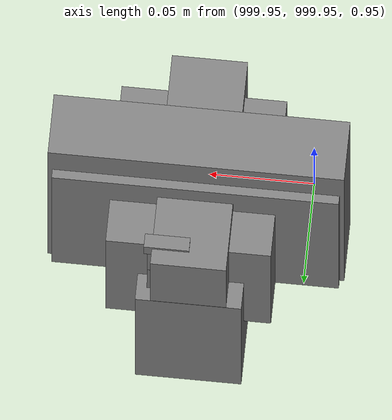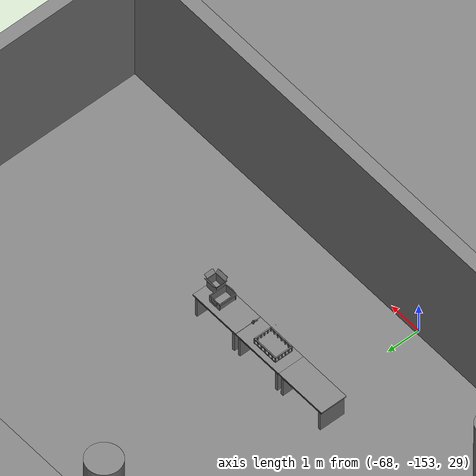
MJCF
<mujoco>
    <option gravity="0.000000000 0.000000000 -9.810000420" timestep="0.0049999999" integrator="implicitfast" density="1.225" viscosity="1.8000001e-05" noslip_iterations="10" iterations="100" sdf_iterations="50">
        <flag multiccd="disable"/>
    </option>
    <size memory="1000M"/>
    <compiler coordinate="local"/>
    <worldbody>
        <light cutoff="30" pos="0 1 1" dir="0 -1 -2"/>
        <light cutoff="30" pos="0 -1 1" dir="0 1 -2"/>
        <body pos="-64.866622925 -149.383972168 30.183746338" euler="89.999984741 89.999946594 0.000000000" name="openloong_gripper_2f85_fix_base_usda_bluebox_01">
            <geom contype="1" conaffinity="1" density="1000" type="box" material="" rgba="0.500000000 0.500000000 0.500000000 1.000000000" solimp="0.899999976 0.949999988 0.001000000" friction="1.000000000 0.005000000 0.000100000" solref="0.020000000 1.000000000" margin="0" condim="3" group="0" pos="0.276580811 0.187225342 0.000068665" quat="0.707106948 0.000077471 0.707106352 0.000077486" size="0.100000001 0.057999998 0.010000000" name="openloong_gripper_2f85_fix_base_usda_geom_8986C1BF_D40C_4DC6_AEC4_726CA4C7B849"/>
            <geom contype="1" conaffinity="1" density="1000" type="box" material="" rgba="0.500000000 0.500000000 0.500000000 1.000000000" solimp="0.899999976 0.949999988 0.001000000" friction="1.000000000 0.005000000 0.000100000" solref="0.020000000 1.000000000" margin="0" condim="3" group="0" pos="0.000000000 0.002883911 0.000000000" quat="0.999999881 0.000000000 0.000000000 0.000000000" size="0.254000008 0.003000000 0.172000006" name="openloong_gripper_2f85_fix_base_usda_geom_FC45A835_06CA_4F15_A1E8_564134E5BCF3"/>
            <geom contype="1" conaffinity="1" density="1000" type="box" material="" rgba="0.500000000 0.500000000 0.500000000 1.000000000" solimp="0.899999976 0.949999988 0.001000000" friction="1.000000000 0.005000000 0.000100000" solref="0.020000000 1.000000000" margin="0" condim="3" group="0" pos="0.000000000 0.124874115 0.173484802" quat="0.999796331 0.020176515 -0.000000015 0.000000030" size="0.259999990 0.119999997 0.007000000" name="openloong_gripper_2f85_fix_base_usda_geom_AEFF1DB3_0C49_4F78_A35B_7929A728C98A"/>
            <geom contype="1" conaffinity="1" density="1000" type="box" material="" rgba="0.500000000 0.500000000 0.500000000 1.000000000" solimp="0.899999976 0.949999988 0.001000000" friction="1.000000000 0.005000000 0.000100000" solref="0.020000000 1.000000000" margin="0" condim="3" group="0" pos="0.000000000 0.124874115 -0.173469543" quat="0.999796331 -0.020176545 -0.000000015 0.000000000" size="0.259999990 0.119999997 0.007000000" name="openloong_gripper_2f85_fix_base_usda_geom_40A85ED2_90D9_44B1_8F49_7B7DBBAE680C"/>
            <geom contype="1" conaffinity="1" density="1000" type="box" material="" rgba="0.500000000 0.500000000 0.500000000 1.000000000" solimp="0.899999976 0.949999988 0.001000000" friction="1.000000000 0.005000000 0.000100000" solref="0.020000000 1.000000000" margin="0" condim="3" group="0" pos="0.000000000 0.214008331 0.188980103" quat="0.999912977 0.013176724 0.000000015 0.000000000" size="0.259999990 0.029999999 0.012500000" name="openloong_gripper_2f85_fix_base_usda_geom_D6B29361_609F_4FB5_9925_F35BD9AEA4DA"/>
            <geom contype="1" conaffinity="1" density="1000" type="box" material="" rgba="0.500000000 0.500000000 0.500000000 1.000000000" solimp="0.899999976 0.949999988 0.001000000" friction="1.000000000 0.005000000 0.000100000" solref="0.020000000 1.000000000" margin="0" condim="3" group="0" pos="-0.258361816 0.125289917 0.001876831" quat="0.702796936 -0.020792112 0.710783124 0.020769298" size="0.189999998 0.119999997 0.009000000" name="openloong_gripper_2f85_fix_base_usda_geom_11EE3A61_BAAF_41E2_9CFA_FE938A40C5EC"/>
            <geom contype="1" conaffinity="1" density="1000" type="box" material="" rgba="0.500000000 0.500000000 0.500000000 1.000000000" solimp="0.899999976 0.949999988 0.001000000" friction="1.000000000 0.005000000 0.000100000" solref="0.020000000 1.000000000" margin="0" condim="3" group="0" pos="0.000000000 0.214008331 -0.188980103" quat="0.999912977 -0.013176769 0.000000030 0.000000015" size="0.259999990 0.029999999 0.012500000" name="openloong_gripper_2f85_fix_base_usda_geom_88D57490_229D_47A0_94A1_7936AF93636B"/>
            <geom contype="1" conaffinity="1" density="1000" type="box" material="" rgba="0.500000000 0.500000000 0.500000000 1.000000000" solimp="0.899999976 0.949999988 0.001000000" friction="1.000000000 0.005000000 0.000100000" solref="0.020000000 1.000000000" margin="0" condim="3" group="0" pos="-0.276611328 0.187225342 0.000068665" quat="0.707106650 0.000077441 0.707106709 0.000077456" size="0.100000001 0.057999998 0.010000000" name="openloong_gripper_2f85_fix_base_usda_geom_CE4B070B_383D_40CC_B000_7BCF40D84C62"/>
            <geom contype="1" conaffinity="1" density="1000" type="box" material="" rgba="0.500000000 0.500000000 0.500000000 1.000000000" solimp="0.899999976 0.949999988 0.001000000" friction="1.000000000 0.005000000 0.000100000" solref="0.020000000 1.000000000" margin="0" condim="3" group="0" pos="0.258331299 0.125289917 0.001876831" quat="0.702851415 0.018856421 0.710823774 -0.019329369" size="0.189999998 0.119999997 0.009000000" name="openloong_gripper_2f85_fix_base_usda_geom_A1DA7526_0C97_4DA2_B817_127899C5B754"/>
            <freejoint name="openloong_gripper_2f85_fix_base_usda_bluebox_01_joint"/>
            <site size="0.005000000 0.005000000 0.005000000" rgba="0.500000000 0.500000000 0.500000000 1.000000000" pos="0.000000000 0.000000000 0.000000000" quat="0.999961913 0.008726534 0.000000000 0.000000000" group="0" type="sphere" name="openloong_gripper_2f85_fix_base_usda_bluebox_01site"/>
        </body>
        <body pos="-64.496299744 -149.491867065 30.235729218" euler="0.000000000 0.000000000 89.999946594" name="openloong_gripper_2f85_fix_base_usda_cardboardbox_01">
            <geom contype="1" conaffinity="1" density="1000" type="box" material="" rgba="0.500000000 0.500000000 0.500000000 1.000000000" solimp="0.899999976 0.949999988 0.001000000" friction="1.000000000 0.005000000 0.000100000" solref="0.020000000 1.000000000" margin="0" condim="3" group="0" pos="-0.003166199 -0.004086494 0.005052090" quat="1.000000000 0.000000000 0.000000000 0.000000000" size="0.142499998 0.177500010 0.005000000" name="openloong_gripper_2f85_fix_base_usda_geom_8D2931FE_CDEE_4202_B2A7_F68FBFAB2262"/>
            <geom contype="1" conaffinity="1" density="1000" type="box" material="" rgba="0.500000000 0.500000000 0.500000000 1.000000000" solimp="0.899999976 0.949999988 0.001000000" friction="1.000000000 0.005000000 0.000100000" solref="0.020000000 1.000000000" margin="0" condim="3" group="0" pos="-0.003166199 0.170316696 0.150570869" quat="1.000000000 0.000000000 0.000000000 0.000000000" size="0.142499998 0.005000000 0.149999991" name="openloong_gripper_2f85_fix_base_usda_geom_6902852F_AE2F_4275_A0D3_9C3CED6D0A84"/>
            <geom contype="1" conaffinity="1" density="1000" type="box" material="" rgba="0.500000000 0.500000000 0.500000000 1.000000000" solimp="0.899999976 0.949999988 0.001000000" friction="1.000000000 0.005000000 0.000100000" solref="0.020000000 1.000000000" margin="0" condim="3" group="0" pos="-0.147399902 -0.005307198 0.150570869" quat="1.000000000 0.000000000 0.000000000 0.000000000" size="0.005000000 0.177500010 0.149999991" name="openloong_gripper_2f85_fix_base_usda_geom_74A1965E_D06C_4C7F_98BC_7AA543C2E1D7"/>
            <geom contype="1" conaffinity="1" density="1000" type="box" material="" rgba="0.500000000 0.500000000 0.500000000 1.000000000" solimp="0.899999976 0.949999988 0.001000000" friction="1.000000000 0.005000000 0.000100000" solref="0.020000000 1.000000000" margin="0" condim="3" group="0" pos="0.140275955 -0.005307198 0.150570869" quat="1.000000000 0.000000000 0.000000000 0.000000000" size="0.005000000 0.177500010 0.149999991" name="openloong_gripper_2f85_fix_base_usda_geom_43B96E0B_A964_4705_855F_F28862A662CD"/>
            <geom contype="1" conaffinity="1" density="1000" type="box" material="" rgba="0.500000000 0.500000000 0.500000000 1.000000000" solimp="0.899999976 0.949999988 0.001000000" friction="1.000000000 0.005000000 0.000100000" solref="0.020000000 1.000000000" margin="0" condim="3" group="0" pos="-0.003166199 -0.181550980 0.150570869" quat="1.000000000 0.000000000 0.000000000 0.000000000" size="0.142499998 0.005000000 0.149999991" name="openloong_gripper_2f85_fix_base_usda_geom_61CBEA5C_D689_4606_8FEE_1823D3AEFA8C"/>
            <freejoint name="openloong_gripper_2f85_fix_base_usda_cardboardbox_01_joint"/>
            <site size="0.005000000 0.005000000 0.005000000" rgba="0.500000000 0.500000000 0.500000000 1.000000000" pos="0.000000000 0.000000000 0.000000000" quat="0.999961913 0.008726535 0.000000000 0.000000000" group="0" type="sphere" name="openloong_gripper_2f85_fix_base_usda_site_99EA067F_E460_431E_BE16_6DA94C335310"/>
            <body pos="0.139160156 -0.004048347 0.301930904" euler="-179.999954224 49.383502960 179.999954224" name="openloong_gripper_2f85_fix_base_usda_A1_006">
                <geom contype="1" conaffinity="1" density="1000" type="box" material="" rgba="0.500000000 0.500000000 0.500000000 1.000000000" solimp="0.899999976 0.949999988 0.001000000" friction="1.000000000 0.005000000 0.000100000" solref="0.020000000 1.000000000" margin="0" condim="3" group="0" pos="-0.071587563 0.000009537 0.001745224" quat="0.999999881 0.000000000 0.000000000 0.000000000" size="0.071249999 0.179999992 0.002500000" name="openloong_gripper_2f85_fix_base_usda_geom_E89BAD98_E7EB_4AB5_AA94_89E0E7C402FE"/>
                <joint armature="0" stiffness="0.07" damping="0.0099999998" axis="0.000000 1.000000 0.000000" type="hinge" name="openloong_gripper_2f85_fix_base_usda_A1_006"/>
            </body>
            <body pos="-0.145902634 -0.004086494 0.301938057" euler="-180.000000000 -60.000011444 -180.000000000" name="openloong_gripper_2f85_fix_base_usda_A2_006">
                <geom contype="1" conaffinity="1" density="1000" type="box" material="" rgba="0.500000000 0.500000000 0.500000000 1.000000000" solimp="0.899999976 0.949999988 0.001000000" friction="1.000000000 0.005000000 0.000100000" solref="0.020000000 1.000000000" margin="0" condim="3" group="0" pos="0.071268082 0.000009537 0.002717972" quat="0.000002921 0.000000000 -0.000000030 0.999999881" size="0.071249999 0.179999992 0.002500000" name="openloong_gripper_2f85_fix_base_usda_geom_6CA83BF1_AF3A_4A0C_A814_30D0646CD52B"/>
                <joint armature="0" stiffness="0.07" damping="0.0099999998" axis="0.000000 1.000000 0.000000" type="hinge" name="openloong_gripper_2f85_fix_base_usda_A2_006"/>
            </body>
            <body pos="-0.003385544 0.175991058 0.301930904" euler="-125.858116150 -0.000004561 0.000002331" name="openloong_gripper_2f85_fix_base_usda_B2_006">
                <geom contype="1" conaffinity="1" density="1000" type="box" material="" rgba="0.500000000 0.500000000 0.500000000 1.000000000" solimp="0.899999976 0.949999988 0.001000000" friction="1.000000000 0.005000000 0.000100000" solref="0.020000000 1.000000000" margin="0" condim="3" group="0" pos="0.000009537 -0.070939064 -0.002470016" quat="0.999614120 0.027776197 -0.000000015 0.000000030" size="0.137500003 0.064999998 0.005000000" name="openloong_gripper_2f85_fix_base_usda_geom_EB4483C4_CC6C_4602_88F8_7E02B0499516"/>
                <joint armature="0" stiffness="0.07" damping="0.0099999998" axis="1.000000 0.000000 0.000000" type="hinge" name="openloong_gripper_2f85_fix_base_usda_B2_006"/>
            </body>
            <body pos="-0.003385544 -0.184140205 0.301938057" euler="147.805557251 0.000000000 0.000000000" name="openloong_gripper_2f85_fix_base_usda_B1_006">
                <geom contype="1" conaffinity="1" density="1000" type="box" material="" rgba="0.500000000 0.500000000 0.500000000 1.000000000" solimp="0.899999976 0.949999988 0.001000000" friction="1.000000000 0.005000000 0.000100000" solref="0.020000000 1.000000000" margin="0" condim="3" group="0" pos="-0.000028610 0.070202351 -0.002703667" quat="0.999614179 -0.027776167 0.000000000 0.000000000" size="0.137500003 0.064999998 0.005000000" name="openloong_gripper_2f85_fix_base_usda_geom_45645ABD_21AC_47A9_B77B_FB351E2A23E7"/>
                <joint armature="0" stiffness="0.07" damping="0.0099999998" axis="1.000000 0.000000 0.000000" type="hinge" name="openloong_gripper_2f85_fix_base_usda_B1_006"/>
            </body>
        </body>
        <body pos="-65.882858276 -149.481979370 30.229999542" euler="-64.487716675 0.000000000 0.000000000" name="openloong_gripper_2f85_fix_base_usda_Barcode">
            <geom contype="1" conaffinity="1" density="1000" type="box" material="" rgba="0.500000000 0.500000000 0.500000000 1.000000000" solimp="0.899999976 0.949999988 0.001000000" friction="1.000000000 0.005000000 0.000100000" solref="0.020000000 1.000000000" margin="0" condim="3" group="0" pos="0.000000000 0.013038635 0.001419067" quat="0.000000000 0.000000000 0.000000000 1.000000119" size="0.034000002 0.010000000 0.017999999" name="openloong_gripper_2f85_fix_base_usda_geom_742DEAF5_91D8_4930_8AA1_C4D1008F1817"/>
            <geom contype="1" conaffinity="1" density="1000" type="box" material="" rgba="0.500000000 0.500000000 0.500000000 1.000000000" solimp="0.899999976 0.949999988 0.001000000" friction="1.000000000 0.005000000 0.000100000" solref="0.020000000 1.000000000" margin="0" condim="3" group="0" pos="0.000000000 -0.035301208 -0.007095337" quat="0.000000000 0.000000000 -0.043619365 0.999048233" size="0.028999999 0.010000000 0.020000000" name="openloong_gripper_2f85_fix_base_usda_geom_F82295F5_BDD7_4CB3_9DBF_BCFB34383987"/>
            <geom contype="1" conaffinity="1" density="1000" type="box" material="" rgba="0.500000000 0.500000000 0.500000000 1.000000000" solimp="0.899999976 0.949999988 0.001000000" friction="1.000000000 0.005000000 0.000100000" solref="0.020000000 1.000000000" margin="0" condim="3" group="0" pos="0.000000000 -0.043411255 -0.011749268" quat="0.922262907 0.386563420 0.000000000 0.000000000" size="0.026000001 0.010000000 0.020000000" name="openloong_gripper_2f85_fix_base_usda_geom_02E61134_CD55_497C_BA61_20848E1ABFA5"/>
            <geom contype="1" conaffinity="1" density="1000" type="box" material="" rgba="0.500000000 0.500000000 0.500000000 1.000000000" solimp="0.899999976 0.949999988 0.001000000" friction="1.000000000 0.005000000 0.000100000" solref="0.020000000 1.000000000" margin="0" condim="3" group="0" pos="0.000000000 -0.016967773 -0.031860352" quat="0.000000000 0.000000000 0.000000000 1.000000119" size="0.008000000 0.010000000 0.013000000" name="openloong_gripper_2f85_fix_base_usda_geom_2E469621_984B_4708_899C_070A155462B7"/>
            <geom contype="1" conaffinity="1" density="1000" type="box" material="" rgba="0.500000000 0.500000000 0.500000000 1.000000000" solimp="0.899999976 0.949999988 0.001000000" friction="1.000000000 0.005000000 0.000100000" solref="0.020000000 1.000000000" margin="0" condim="3" group="0" pos="0.000000000 -0.001869202 0.000312805" quat="0.953716993 0.300705761 0.000000000 0.000000000" size="0.032000002 0.010000000 0.018999999" name="openloong_gripper_2f85_fix_base_usda_geom_0A11CBC3_DF9E_4773_8C1E_A35801021E29"/>
            <geom contype="1" conaffinity="1" density="1000" type="box" material="" rgba="0.500000000 0.500000000 0.500000000 1.000000000" solimp="0.899999976 0.949999988 0.001000000" friction="1.000000000 0.005000000 0.000100000" solref="0.020000000 1.000000000" margin="0" condim="3" group="0" pos="0.000000000 -0.019531250 -0.003173828" quat="0.953716993 0.300705761 0.000000000 0.000000000" size="0.030999999 0.010000000 0.020000000" name="openloong_gripper_2f85_fix_base_usda_geom_3D58A194_3B34_4976_9E1F_9A4DAAE3BFF0"/>
            <geom contype="1" conaffinity="1" density="1000" type="box" material="" rgba="0.500000000 0.500000000 0.500000000 1.000000000" solimp="0.899999976 0.949999988 0.001000000" friction="1.000000000 0.005000000 0.000100000" solref="0.020000000 1.000000000" margin="0" condim="3" group="0" pos="0.000000000 -0.035301208 -0.007095337" quat="0.953716993 0.300705761 0.000000000 0.000000000" size="0.028999999 0.010000000 0.020000000" name="openloong_gripper_2f85_fix_base_usda_geom_2E1CDF10_72F7_4106_A330_AB97BCD73CFC"/>
            <geom contype="1" conaffinity="1" density="1000" type="box" material="" rgba="0.500000000 0.500000000 0.500000000 1.000000000" solimp="0.899999976 0.949999988 0.001000000" friction="1.000000000 0.005000000 0.000100000" solref="0.020000000 1.000000000" margin="0" condim="3" group="0" pos="0.000000000 -0.042617798 -0.071121216" quat="0.000000000 0.000000000 0.000000000 1.000000119" size="0.013000000 0.021000000 0.059999999" name="openloong_gripper_2f85_fix_base_usda_geom_D55E119B_FA81_4025_B70C_05963C7792A5"/>
            <freejoint name="openloong_gripper_2f85_fix_base_usda_Barcode_joint"/>
            <site size="0.005000000 0.005000000 0.005000000" rgba="0.500000000 0.500000000 0.500000000 1.000000000" pos="0.000000000 0.000000000 0.000000000" quat="1.000000000 0.000000000 0.000000000 0.000000000" group="0" type="sphere" name="openloong_gripper_2f85_fix_base_usda_Barcode_site"/>
        </body>
        <body pos="-66.745018005 -149.392349243 30.184000015" euler="0.000000000 0.000000000 89.999946594" name="[22330235183719]_Basket_01">
            <geom contype="1" conaffinity="1" density="1000" type="box" material="" rgba="0.500000000 0.500000000 0.500000000 1.000000000" solimp="0.899999976 0.949999988 0.001000000" friction="1.000000000 0.005000000 0.000100000" solref="0.020000000 1.000000000" margin="0" condim="3" group="0" pos="-0.052425385 0.389207840 0.089787483" quat="0.707107008 0.000000000 0.000000000 0.707106411" size="0.014249999 0.014249999 0.059999999" name="[22330235183719]_geom_B051A465_EFAD_4F26_B59D_1263BD82AC44"/>
            <geom contype="1" conaffinity="1" density="1000" type="box" material="" rgba="0.500000000 0.500000000 0.500000000 1.000000000" solimp="0.899999976 0.949999988 0.001000000" friction="1.000000000 0.005000000 0.000100000" solref="0.020000000 1.000000000" margin="0" condim="3" group="0" pos="0.264015198 -0.133043289 0.089787483" quat="0.707107008 0.000000000 0.000000000 0.707106411" size="0.014249999 0.014249999 0.059999999" name="[22330235183719]_geom_F8B1A8E6_A72D_412A_9F39_1A0F870437D6"/>
            <geom contype="1" conaffinity="1" density="1000" type="box" material="" rgba="0.500000000 0.500000000 0.500000000 1.000000000" solimp="0.899999976 0.949999988 0.001000000" friction="1.000000000 0.005000000 0.000100000" solref="0.020000000 1.000000000" margin="0" condim="3" group="0" pos="-0.264015198 -0.265548706 0.089793205" quat="0.707107008 0.000000000 0.000000000 0.707106411" size="0.014249999 0.014249999 0.059999999" name="[22330235183719]_geom_B73E0F29_8FC8_4697_8262_5C87DF453BBD"/>
            <geom contype="1" conaffinity="1" density="1000" type="box" material="" rgba="0.500000000 0.500000000 0.500000000 1.000000000" solimp="0.899999976 0.949999988 0.001000000" friction="1.000000000 0.005000000 0.000100000" solref="0.020000000 1.000000000" margin="0" condim="3" group="0" pos="-0.160263062 -0.389322281 0.089793205" quat="0.707107008 0.000000000 0.000000000 0.707106411" size="0.014249999 0.014249999 0.059999999" name="[22330235183719]_geom_19CE997F_BD53_4435_B80B_6EEE1E1A459B"/>
            <geom contype="1" conaffinity="1" density="1000" type="box" material="" rgba="0.500000000 0.500000000 0.500000000 1.000000000" solimp="0.899999976 0.949999988 0.001000000" friction="1.000000000 0.005000000 0.000100000" solref="0.020000000 1.000000000" margin="0" condim="3" group="0" pos="0.162265778 -0.389322281 0.089787483" quat="0.707107008 0.000000000 0.000000000 0.707106411" size="0.014249999 0.014249999 0.059999999" name="[22330235183719]_geom_0003514E_4A51_4863_9CD7_36B388401150"/>
            <geom contype="1" conaffinity="1" density="1000" type="box" material="" rgba="0.500000000 0.500000000 0.500000000 1.000000000" solimp="0.899999976 0.949999988 0.001000000" friction="1.000000000 0.005000000 0.000100000" solref="0.020000000 1.000000000" margin="0" condim="3" group="0" pos="0.264015198 0.389207840 0.089787483" quat="0.707107008 0.000000000 0.000000000 0.707106411" size="0.014249999 0.014249999 0.059999999" name="[22330235183719]_geom_92FC122C_09FC_4216_8E06_FE6A373CD4B8"/>
            <geom contype="1" conaffinity="1" density="1000" type="box" material="" rgba="0.500000000 0.500000000 0.500000000 1.000000000" solimp="0.899999976 0.949999988 0.001000000" friction="1.000000000 0.005000000 0.000100000" solref="0.020000000 1.000000000" margin="0" condim="3" group="0" pos="-0.264015198 -0.133043289 0.089793205" quat="0.707107008 0.000000000 0.000000000 0.707106411" size="0.014249999 0.014249999 0.059999999" name="[22330235183719]_geom_D2790E73_D1F6_43A2_AD1A_F4546D82C3A6"/>
            <geom contype="1" conaffinity="1" density="1000" type="box" material="" rgba="0.500000000 0.500000000 0.500000000 1.000000000" solimp="0.899999976 0.949999988 0.001000000" friction="1.000000000 0.005000000 0.000100000" solref="0.020000000 1.000000000" margin="0" condim="3" group="0" pos="-0.264026642 0.269256592 0.089793205" quat="0.707107008 0.000000000 0.000000000 0.707106411" size="0.014249999 0.014249999 0.059999999" name="[22330235183719]_geom_5342F0E9_6DD8_4BCE_BD0F_89FCCAC025DF"/>
            <geom contype="1" conaffinity="1" density="1000" type="box" material="" rgba="0.500000000 0.500000000 0.500000000 1.000000000" solimp="0.899999976 0.949999988 0.001000000" friction="1.000000000 0.005000000 0.000100000" solref="0.020000000 1.000000000" margin="0" condim="3" group="0" pos="0.054462433 0.389207840 0.089787483" quat="0.707107008 0.000000000 0.000000000 0.707106411" size="0.014249999 0.014249999 0.059999999" name="[22330235183719]_geom_36D321DC_AA03_46CD_872A_70D427372E81"/>
            <geom contype="1" conaffinity="1" density="1000" type="box" material="" rgba="0.500000000 0.500000000 0.500000000 1.000000000" solimp="0.899999976 0.949999988 0.001000000" friction="1.000000000 0.005000000 0.000100000" solref="0.020000000 1.000000000" margin="0" condim="3" group="0" pos="0.054462433 -0.389322281 0.089787483" quat="0.707107008 0.000000000 0.000000000 0.707106411" size="0.014249999 0.014249999 0.059999999" name="[22330235183719]_geom_CD5E077F_6A36_4B88_AFCB_424C4EB17166"/>
            <geom contype="1" conaffinity="1" density="1000" type="box" material="" rgba="0.500000000 0.500000000 0.500000000 1.000000000" solimp="0.899999976 0.949999988 0.001000000" friction="1.000000000 0.005000000 0.000100000" solref="0.020000000 1.000000000" margin="0" condim="3" group="0" pos="0.264015198 0.269256592 0.089793205" quat="0.707107008 0.000000000 0.000000000 0.707106411" size="0.014249999 0.014249999 0.059999999" name="[22330235183719]_geom_72200FEA_EEF7_408F_97FC_7EEDD84B9788"/>
            <geom contype="1" conaffinity="1" density="1000" type="box" material="" rgba="0.500000000 0.500000000 0.500000000 1.000000000" solimp="0.899999976 0.949999988 0.001000000" friction="1.000000000 0.005000000 0.000100000" solref="0.020000000 1.000000000" margin="0" condim="3" group="0" pos="0.264015198 -0.389322281 0.089787483" quat="0.707107008 0.000000000 0.000000000 0.707106411" size="0.014249999 0.014249999 0.059999999" name="[22330235183719]_geom_8A47F847_462E_4B85_B001_D23DEDFB2A8D"/>
            <geom contype="1" conaffinity="1" density="1000" type="box" material="" rgba="0.500000000 0.500000000 0.500000000 1.000000000" solimp="0.899999976 0.949999988 0.001000000" friction="1.000000000 0.005000000 0.000100000" solref="0.020000000 1.000000000" margin="0" condim="3" group="0" pos="0.000000000 0.000000000 0.015998840" quat="0.707107008 0.000000000 0.000000000 0.707106411" size="0.403499991 0.279000014 0.015750000" name="[22330235183719]_geom_28854990_5E00_4BBF_8B29_FDCEC6049039"/>
            <geom contype="1" conaffinity="1" density="1000" type="box" material="" rgba="0.500000000 0.500000000 0.500000000 1.000000000" solimp="0.899999976 0.949999988 0.001000000" friction="1.000000000 0.005000000 0.000100000" solref="0.020000000 1.000000000" margin="0" condim="3" group="0" pos="0.000000000 -0.389476776 0.163619041" quat="0.707107008 0.000000000 0.000000000 0.707106411" size="0.015000000 0.277500004 0.015750000" name="[22330235183719]_geom_E3154CBF_B1FD_46C3_A9A5_ACFA5EBF13F8"/>
            <geom contype="1" conaffinity="1" density="1000" type="box" material="" rgba="0.500000000 0.500000000 0.500000000 1.000000000" solimp="0.899999976 0.949999988 0.001000000" friction="1.000000000 0.005000000 0.000100000" solref="0.020000000 1.000000000" margin="0" condim="3" group="0" pos="0.162265778 0.389207840 0.089787483" quat="0.707107008 0.000000000 0.000000000 0.707106411" size="0.014249999 0.014249999 0.059999999" name="[22330235183719]_geom_7EB1EB63_AAE0_461F_AC8F_A5FB923E7AD0"/>
            <geom contype="1" conaffinity="1" density="1000" type="box" material="" rgba="0.500000000 0.500000000 0.500000000 1.000000000" solimp="0.899999976 0.949999988 0.001000000" friction="1.000000000 0.005000000 0.000100000" solref="0.020000000 1.000000000" margin="0" condim="3" group="0" pos="0.000000000 0.389471054 0.163619041" quat="0.707107008 0.000000000 0.000000000 0.707106411" size="0.015000000 0.277500004 0.015750000" name="[22330235183719]_geom_F12EC56E_0A70_4C55_89BF_03C92A58AC11"/>
            <geom contype="1" conaffinity="1" density="1000" type="box" material="" rgba="0.500000000 0.500000000 0.500000000 1.000000000" solimp="0.899999976 0.949999988 0.001000000" friction="1.000000000 0.005000000 0.000100000" solref="0.020000000 1.000000000" margin="0" condim="3" group="0" pos="-0.263511658 0.000000000 0.163619041" quat="0.707107008 0.000000000 0.000000000 0.707106411" size="0.403499991 0.015000000 0.015750000" name="[22330235183719]_geom_87A2CCE4_5F27_4AD9_A46F_35246B134936"/>
            <geom contype="1" conaffinity="1" density="1000" type="box" material="" rgba="0.500000000 0.500000000 0.500000000 1.000000000" solimp="0.899999976 0.949999988 0.001000000" friction="1.000000000 0.005000000 0.000100000" solref="0.020000000 1.000000000" margin="0" condim="3" group="0" pos="-0.264015198 0.141334534 0.089793205" quat="0.707107008 0.000000000 0.000000000 0.707106411" size="0.014249999 0.014249999 0.059999999" name="[22330235183719]_geom_17A981F7_DCAA_4413_B940_57F66EFEAEEC"/>
            <geom contype="1" conaffinity="1" density="1000" type="box" material="" rgba="0.500000000 0.500000000 0.500000000 1.000000000" solimp="0.899999976 0.949999988 0.001000000" friction="1.000000000 0.005000000 0.000100000" solref="0.020000000 1.000000000" margin="0" condim="3" group="0" pos="0.264015198 -0.265548706 0.089787483" quat="0.707107008 0.000000000 0.000000000 0.707106411" size="0.014249999 0.014249999 0.059999999" name="[22330235183719]_geom_9569EFA5_4226_44A7_B308_E347F7C48768"/>
            <geom contype="1" conaffinity="1" density="1000" type="box" material="" rgba="0.500000000 0.500000000 0.500000000 1.000000000" solimp="0.899999976 0.949999988 0.001000000" friction="1.000000000 0.005000000 0.000100000" solref="0.020000000 1.000000000" margin="0" condim="3" group="0" pos="-0.160263062 0.389207840 0.089787483" quat="0.707107008 0.000000000 0.000000000 0.707106411" size="0.014249999 0.014249999 0.059999999" name="[22330235183719]_geom_155FF79B_5BF0_45AF_8985_B6AD8D050864"/>
            <geom contype="1" conaffinity="1" density="1000" type="box" material="" rgba="0.500000000 0.500000000 0.500000000 1.000000000" solimp="0.899999976 0.949999988 0.001000000" friction="1.000000000 0.005000000 0.000100000" solref="0.020000000 1.000000000" margin="0" condim="3" group="0" pos="-0.052425385 -0.389322281 0.089787483" quat="0.707107008 0.000000000 0.000000000 0.707106411" size="0.014249999 0.014249999 0.059999999" name="[22330235183719]_geom_13E3823A_F237_4A34_B393_7E2589B5D3BA"/>
            <geom contype="1" conaffinity="1" density="1000" type="box" material="" rgba="0.500000000 0.500000000 0.500000000 1.000000000" solimp="0.899999976 0.949999988 0.001000000" friction="1.000000000 0.005000000 0.000100000" solref="0.020000000 1.000000000" margin="0" condim="3" group="0" pos="-0.264026642 -0.389322281 0.089793205" quat="0.707107008 0.000000000 0.000000000 0.707106411" size="0.014249999 0.014249999 0.059999999" name="[22330235183719]_geom_D42DEFA5_9599_4ED9_9276_1BD97662661B"/>
            <geom contype="1" conaffinity="1" density="1000" type="box" material="" rgba="0.500000000 0.500000000 0.500000000 1.000000000" solimp="0.899999976 0.949999988 0.001000000" friction="1.000000000 0.005000000 0.000100000" solref="0.020000000 1.000000000" margin="0" condim="3" group="0" pos="0.264015198 0.141334534 0.089787483" quat="0.707107008 0.000000000 0.000000000 0.707106411" size="0.014249999 0.014249999 0.059999999" name="[22330235183719]_geom_DA04DF9E_422D_45A9_975D_7D608C708278"/>
            <geom contype="1" conaffinity="1" density="1000" type="box" material="" rgba="0.500000000 0.500000000 0.500000000 1.000000000" solimp="0.899999976 0.949999988 0.001000000" friction="1.000000000 0.005000000 0.000100000" solref="0.020000000 1.000000000" margin="0" condim="3" group="0" pos="-0.264015198 0.389207840 0.089793205" quat="0.707107008 0.000000000 0.000000000 0.707106411" size="0.014249999 0.014249999 0.059999999" name="[22330235183719]_geom_FEA047F8_A3D6_463B_9DCD_6D8F3E966CD7"/>
            <geom contype="1" conaffinity="1" density="1000" type="box" material="" rgba="0.500000000 0.500000000 0.500000000 1.000000000" solimp="0.899999976 0.949999988 0.001000000" friction="1.000000000 0.005000000 0.000100000" solref="0.020000000 1.000000000" margin="0" condim="3" group="0" pos="0.264015198 0.004480362 0.089787483" quat="0.707107008 0.000000000 0.000000000 0.707106411" size="0.014249999 0.014249999 0.059999999" name="[22330235183719]_geom_273B6F2C_5D7D_4346_A2DC_99868D2AA0DB"/>
            <geom contype="1" conaffinity="1" density="1000" type="box" material="" rgba="0.500000000 0.500000000 0.500000000 1.000000000" solimp="0.899999976 0.949999988 0.001000000" friction="1.000000000 0.005000000 0.000100000" solref="0.020000000 1.000000000" margin="0" condim="3" group="0" pos="0.263694763 -0.000011444 0.163619041" quat="0.707107008 0.000000000 0.000000000 0.707106411" size="0.403499991 0.015000000 0.015750000" name="[22330235183719]_geom_B8E7026A_2A95_4499_8992_090200D420FB"/>
            <geom contype="1" conaffinity="1" density="1000" type="box" material="" rgba="0.500000000 0.500000000 0.500000000 1.000000000" solimp="0.899999976 0.949999988 0.001000000" friction="1.000000000 0.005000000 0.000100000" solref="0.020000000 1.000000000" margin="0" condim="3" group="0" pos="-0.264015198 0.004480362 0.089793205" quat="0.707107008 0.000000000 0.000000000 0.707106411" size="0.014249999 0.014249999 0.059999999" name="[22330235183719]_geom_203D0A7A_B43C_432B_862F_68FF611FD6CD"/>
            <freejoint name="[22330235183719]_joint_A7B6D729_EA2D_4ECC_92C6_37CDDDD47994"/>
        </body>
        <body pos="0.000000000 0.000000000 0.000000000" euler="0.000000000 0.000000000 0.000000000" name="Static Objects_Static Objects">
            <geom contype="1" conaffinity="1" density="1000" type="box" material="" rgba="0.500000000 0.500000000 0.500000000 1.000000000" solimp="0.899999976 0.949999988 0.001000000" friction="1.000000000 0.005000000 0.000100000" solref="0.020000000 1.000000000" margin="0" condim="3" group="0" pos="-67.544113159 -149.365814209 29.727830887" quat="0.500000417 0.499999970 0.499999553 0.499999970" size="0.381000012 0.319999993 0.041000001" name="Static Objects_geom_A2C5A84F_F4C6_4CB5_B56B_C32055805243"/>
            <geom contype="1" conaffinity="1" density="1000" type="box" material="" rgba="0.500000000 0.500000000 0.500000000 1.000000000" solimp="0.899999976 0.949999988 0.001000000" friction="1.000000000 0.005000000 0.000100000" solref="0.020000000 1.000000000" margin="0" condim="3" group="0" pos="-68.239501953 -149.365814209 30.086868286" quat="0.500000417 0.499999970 0.499999553 0.499999970" size="0.370999992 0.039500002 0.745000005" name="Static Objects_geom_24E09B8B_F4D5_4BA6_8A46_BB13D094E586"/>
            <geom contype="1" conaffinity="1" density="1000" type="box" material="" rgba="0.500000000 0.500000000 0.500000000 1.000000000" solimp="0.899999976 0.949999988 0.001000000" friction="1.000000000 0.005000000 0.000100000" solref="0.020000000 1.000000000" margin="0" condim="3" group="0" pos="-68.239501953 -149.365814209 30.147235870" quat="0.500000417 0.499999970 0.499999553 0.499999970" size="0.400000006 0.022000000 0.800000012" name="Static Objects_geom_4508A49D_BA28_401B_9C31_4309C84FF0D2"/>
            <geom contype="1" conaffinity="1" density="1000" type="box" material="" rgba="0.500000000 0.500000000 0.500000000 1.000000000" solimp="0.899999976 0.949999988 0.001000000" friction="1.000000000 0.005000000 0.000100000" solref="0.020000000 1.000000000" margin="0" condim="3" group="0" pos="-68.934890747 -149.365814209 29.727830887" quat="0.500000417 0.499999970 0.499999553 0.499999970" size="0.381000012 0.319999993 0.041000001" name="Static Objects_geom_1DC104E8_ACD7_419D_BF62_1499163DCFA2"/>
            <geom contype="1" conaffinity="1" density="1000" type="box" material="" rgba="0.500000000 0.500000000 0.500000000 1.000000000" solimp="0.899999976 0.949999988 0.001000000" friction="1.000000000 0.005000000 0.000100000" solref="0.020000000 1.000000000" margin="0" condim="3" group="0" pos="-68.239501953 -149.365814209 29.561563492" quat="0.500000417 0.499999970 0.499999553 0.499999970" size="0.020000000 0.022000000 0.660000026" name="Static Objects_geom_77F1C5C0_C640_4B2E_A6FB_DDF6DF1CE5F6"/>
            <geom contype="1" conaffinity="1" density="1000" type="box" material="" rgba="0.500000000 0.500000000 0.500000000 1.000000000" solimp="0.899999976 0.949999988 0.001000000" friction="1.000000000 0.005000000 0.000100000" solref="0.020000000 1.000000000" margin="0" condim="3" group="0" pos="-65.945671082 -149.365814209 29.727830887" quat="0.500000417 0.499999970 0.499999553 0.499999970" size="0.381000012 0.319999993 0.041000001" name="Static Objects_geom_7BAAC299_EF98_4B97_9B9F_D339C0B52D57"/>
            <geom contype="1" conaffinity="1" density="1000" type="box" material="" rgba="0.500000000 0.500000000 0.500000000 1.000000000" solimp="0.899999976 0.949999988 0.001000000" friction="1.000000000 0.005000000 0.000100000" solref="0.020000000 1.000000000" margin="0" condim="3" group="0" pos="-66.641059875 -149.365814209 30.086868286" quat="0.500000417 0.499999970 0.499999553 0.499999970" size="0.370999992 0.039500002 0.745000005" name="Static Objects_geom_81F8ABF4_9D7A_4841_A381_02A966B7679A"/>
            <geom contype="1" conaffinity="1" density="1000" type="box" material="" rgba="0.500000000 0.500000000 0.500000000 1.000000000" solimp="0.899999976 0.949999988 0.001000000" friction="1.000000000 0.005000000 0.000100000" solref="0.020000000 1.000000000" margin="0" condim="3" group="0" pos="-66.641059875 -149.365814209 30.147235870" quat="0.500000417 0.499999970 0.499999553 0.499999970" size="0.400000006 0.022000000 0.800000012" name="Static Objects_geom_C2DF4D06_55D1_46EC_9A75_70C07171781F"/>
            <geom contype="1" conaffinity="1" density="1000" type="box" material="" rgba="0.500000000 0.500000000 0.500000000 1.000000000" solimp="0.899999976 0.949999988 0.001000000" friction="1.000000000 0.005000000 0.000100000" solref="0.020000000 1.000000000" margin="0" condim="3" group="0" pos="-67.336448669 -149.365814209 29.727830887" quat="0.500000417 0.499999970 0.499999553 0.499999970" size="0.381000012 0.319999993 0.041000001" name="Static Objects_geom_BA873740_9AF5_4373_88C5_719952188811"/>
            <geom contype="1" conaffinity="1" density="1000" type="box" material="" rgba="0.500000000 0.500000000 0.500000000 1.000000000" solimp="0.899999976 0.949999988 0.001000000" friction="1.000000000 0.005000000 0.000100000" solref="0.020000000 1.000000000" margin="0" condim="3" group="0" pos="-66.641059875 -149.365814209 29.561563492" quat="0.500000417 0.499999970 0.499999553 0.499999970" size="0.020000000 0.022000000 0.660000026" name="Static Objects_geom_D078D6A1_D874_47EC_8988_FA582F869E8F"/>
            <geom contype="1" conaffinity="1" density="1000" type="box" material="" rgba="0.500000000 0.500000000 0.500000000 1.000000000" solimp="0.899999976 0.949999988 0.001000000" friction="1.000000000 0.005000000 0.000100000" solref="0.020000000 1.000000000" margin="0" condim="3" group="0" pos="-64.338577271 -149.365814209 29.727830887" quat="0.500000417 0.499999970 0.499999553 0.499999970" size="0.381000012 0.319999993 0.041000001" name="Static Objects_geom_A6389ED8_A075_4519_948B_5D4BAE033473"/>
            <geom contype="1" conaffinity="1" density="1000" type="box" material="" rgba="0.500000000 0.500000000 0.500000000 1.000000000" solimp="0.899999976 0.949999988 0.001000000" friction="1.000000000 0.005000000 0.000100000" solref="0.020000000 1.000000000" margin="0" condim="3" group="0" pos="-65.033966064 -149.365814209 30.086868286" quat="0.500000417 0.499999970 0.499999553 0.499999970" size="0.370999992 0.039500002 0.745000005" name="Static Objects_geom_74195E0A_9580_4D31_BEEA_15C9A733910E"/>
            <geom contype="1" conaffinity="1" density="1000" type="box" material="" rgba="0.500000000 0.500000000 0.500000000 1.000000000" solimp="0.899999976 0.949999988 0.001000000" friction="1.000000000 0.005000000 0.000100000" solref="0.020000000 1.000000000" margin="0" condim="3" group="0" pos="-65.033966064 -149.365814209 30.147235870" quat="0.500000417 0.499999970 0.499999553 0.499999970" size="0.400000006 0.022000000 0.800000012" name="Static Objects_geom_CC6AD81D_7B1E_4392_88FC_3F2196E65F0C"/>
            <geom contype="1" conaffinity="1" density="1000" type="box" material="" rgba="0.500000000 0.500000000 0.500000000 1.000000000" solimp="0.899999976 0.949999988 0.001000000" friction="1.000000000 0.005000000 0.000100000" solref="0.020000000 1.000000000" margin="0" condim="3" group="0" pos="-65.729354858 -149.365814209 29.727830887" quat="0.500000417 0.499999970 0.499999553 0.499999970" size="0.381000012 0.319999993 0.041000001" name="Static Objects_geom_DF33359C_0172_4E62_9A74_D8D362E95239"/>
            <geom contype="1" conaffinity="1" density="1000" type="box" material="" rgba="0.500000000 0.500000000 0.500000000 1.000000000" solimp="0.899999976 0.949999988 0.001000000" friction="1.000000000 0.005000000 0.000100000" solref="0.020000000 1.000000000" margin="0" condim="3" group="0" pos="-65.033966064 -149.365814209 29.561563492" quat="0.500000417 0.499999970 0.499999553 0.499999970" size="0.020000000 0.022000000 0.660000026" name="Static Objects_geom_252F3FEE_2D53_4A66_A771_1A17676CC17C"/>
            <geom contype="1" conaffinity="1" density="1000" type="box" material="" rgba="0.500000000 0.500000000 0.500000000 1.000000000" solimp="0.899999976 0.949999988 0.001000000" friction="1.000000000 0.005000000 0.000100000" solref="0.020000000 1.000000000" margin="0" condim="3" group="0" pos="-61.754566193 -137.853729248 33.906845093" quat="0.707107067 0.000000000 0.000000000 0.707106471" size="0.759999990 0.759999990 4.500000000" name="Static Objects_geom_A3F147C4_C41A_453E_9A18_FA7C637A7373"/>
            <geom contype="1" conaffinity="1" density="1000" type="box" material="" rgba="0.500000000 0.500000000 0.500000000 1.000000000" solimp="0.899999976 0.949999988 0.001000000" friction="1.000000000 0.005000000 0.000100000" solref="0.020000000 1.000000000" margin="0" condim="3" group="0" pos="-57.511135101 -144.927108765 31.707921982" quat="1.000000000 0.000000000 0.000000000 0.000000000" size="0.200000003 8.000000000 2.299999952" name="Static Objects_geom_366AFC66_1016_4151_8EEF_64FF8E2F1E31"/>
            <geom contype="1" conaffinity="1" density="1000" type="box" material="" rgba="0.500000000 0.500000000 0.500000000 1.000000000" solimp="0.899999976 0.949999988 0.001000000" friction="1.000000000 0.005000000 0.000100000" solref="0.020000000 1.000000000" margin="0" condim="3" group="0" pos="-80.517646790 -157.574050903 31.688196182" quat="0.707107067 0.000000000 0.000000000 0.707106471" size="0.600000024 0.600000024 2.299999952" name="Static Objects_geom_134DB3B3_087B_4510_8AEA_C519AD83AAD5"/>
            <geom contype="1" conaffinity="1" density="1000" type="box" material="" rgba="0.500000000 0.500000000 0.500000000 1.000000000" solimp="0.899999976 0.949999988 0.001000000" friction="1.000000000 0.005000000 0.000100000" solref="0.020000000 1.000000000" margin="0" condim="3" group="0" pos="-80.711044312 -147.414932251 31.666158676" quat="1.000000000 0.000000000 0.000000000 0.000000000" size="0.200000003 10.000000000 2.299999952" name="Static Objects_geom_2D3AF754_C70A_4DCD_8663_3D0F5AF00AE6"/>
            <geom contype="1" conaffinity="1" density="1000" type="box" material="" rgba="0.500000000 0.500000000 0.500000000 1.000000000" solimp="0.899999976 0.949999988 0.001000000" friction="1.000000000 0.005000000 0.000100000" solref="0.020000000 1.000000000" margin="0" condim="3" group="0" pos="-57.687217712 -137.434692383 31.688196182" quat="0.707107067 0.000000000 0.000000000 0.707106471" size="0.600000024 0.600000024 2.299999952" name="Static Objects_geom_22F72DBA_10F1_4F89_AB6B_E11A25258A58"/>
            <geom contype="1" conaffinity="1" density="1000" type="box" material="" rgba="0.500000000 0.500000000 0.500000000 1.000000000" solimp="0.899999976 0.949999988 0.001000000" friction="1.000000000 0.005000000 0.000100000" solref="0.020000000 1.000000000" margin="0" condim="3" group="0" pos="-69.537033081 -140.263229370 31.714921951" quat="0.707107067 0.000000000 0.000000000 0.707106471" size="0.759999990 4.500000000 2.299999952" name="Static Objects_geom_1F99F7D6_A3E4_450B_A342_04FFB21A96DB"/>
            <geom contype="1" conaffinity="1" density="1000" type="box" material="" rgba="0.500000000 0.500000000 0.500000000 1.000000000" solimp="0.899999976 0.949999988 0.001000000" friction="1.000000000 0.005000000 0.000100000" solref="0.020000000 1.000000000" margin="0" condim="3" group="0" pos="-80.073638916 -137.853713989 33.906845093" quat="0.707107067 0.000000000 0.000000000 0.707106471" size="0.759999990 0.759999990 4.500000000" name="Static Objects_geom_BF9AD813_937F_4177_97F6_79B0B600CB6D"/>
            <geom contype="1" conaffinity="1" density="1000" type="box" material="" rgba="0.500000000 0.500000000 0.500000000 1.000000000" solimp="0.899999976 0.949999988 0.001000000" friction="1.000000000 0.005000000 0.000100000" solref="0.020000000 1.000000000" margin="0" condim="3" group="0" pos="-73.406707764 -155.734664917 31.707921982" quat="1.000000000 0.000000000 0.000000000 0.000000000" size="0.200000003 3.000000000 2.299999952" name="Static Objects_geom_7ED0C33E_2420_4F27_A3A5_038E79A52B80"/>
            <geom contype="1" conaffinity="1" density="1000" type="box" material="" rgba="0.500000000 0.500000000 0.500000000 1.000000000" solimp="0.899999976 0.949999988 0.001000000" friction="1.000000000 0.005000000 0.000100000" solref="0.020000000 1.000000000" margin="0" condim="3" group="0" pos="-68.497543335 -137.448257446 31.707921982" quat="0.707107067 0.000000000 0.000000000 0.707106471" size="0.200000003 14.000000000 2.299999952" name="Static Objects_geom_ABBB5220_0343_46B4_98FC_58915DEE1BD5"/>
            <geom contype="1" conaffinity="1" density="1000" type="cylinder" material="" rgba="0.500000000 0.500000000 0.500000000 1.000000000" solimp="0.899999976 0.949999988 0.001000000" friction="1.000000000 0.005000000 0.000100000" solref="0.020000000 1.000000000" margin="0" condim="3" group="0" pos="-68.868522644 -142.134506226 31.711090088" quat="0.707107067 0.000000000 0.000000000 0.707106471" size="0.509999990 2.299999952 1.000000000" name="Static Objects_geom_6C9724A7_0680_4D38_B954_5F676580272A"/>
            <geom contype="1" conaffinity="1" density="1000" type="plane" material="" rgba="0.500000000 0.500000000 0.500000000 1.000000000" solimp="0.899999976 0.949999988 0.001000000" friction="1.000000000 0.005000000 0.000100000" solref="0.020000000 1.000000000" margin="0" condim="3" group="0" pos="-72.873703003 -147.131927490 29.409669876" quat="1.000000000 0.000000000 0.000000000 0.000000000" size="18.000000000 14.000000000 1.000000000" name="Static Objects_geom_DDFCFEF6_0E08_4132_BEDD_FC4218211BE0"/>
            <geom contype="1" conaffinity="1" density="1000" type="box" material="" rgba="0.500000000 0.500000000 0.500000000 1.000000000" solimp="0.899999976 0.949999988 0.001000000" friction="1.000000000 0.005000000 0.000100000" solref="0.020000000 1.000000000" margin="0" condim="3" group="0" pos="-79.943580627 -157.782272339 31.707921982" quat="0.707107067 0.000000000 0.000000000 0.707106471" size="0.200000003 7.000000000 2.299999952" name="Static Objects_geom_7D373298_778D_4377_86AC_9CC8DD68B9B0"/>
            <geom contype="1" conaffinity="1" density="1000" type="box" material="" rgba="0.500000000 0.500000000 0.500000000 1.000000000" solimp="0.899999976 0.949999988 0.001000000" friction="1.000000000 0.005000000 0.000100000" solref="0.020000000 1.000000000" margin="0" condim="3" group="0" pos="-65.421028137 -152.903442383 31.707921982" quat="0.707107067 0.000000000 0.000000000 0.707106471" size="0.200000003 7.800000191 2.299999952" name="Static Objects_geom_7C04E676_2AF0_4DB0_A5F6_346326C44E99"/>
            <geom contype="1" conaffinity="1" density="1000" type="box" material="" rgba="0.500000000 0.500000000 0.500000000 1.000000000" solimp="0.899999976 0.949999988 0.001000000" friction="1.000000000 0.005000000 0.000100000" solref="0.020000000 1.000000000" margin="0" condim="3" group="0" pos="-74.776908875 -149.964416504 31.688196182" quat="1.000000000 0.000000000 0.000000000 0.000000000" size="0.600000024 0.409999996 2.299999952" name="Static Objects_geom_28FD4045_B3F3_4B2D_BA1D_E176D7A44635"/>
            <geom contype="1" conaffinity="1" density="1000" type="cylinder" material="" rgba="0.500000000 0.500000000 0.500000000 1.000000000" solimp="0.899999976 0.949999988 0.001000000" friction="1.000000000 0.005000000 0.000100000" solref="0.020000000 1.000000000" margin="0" condim="3" group="0" pos="-60.161884308 -142.134506226 31.711090088" quat="0.707107067 0.000000000 0.000000000 0.707106471" size="0.509999990 2.299999952 1.000000000" name="Static Objects_geom_E8EE1044_D91A_4FC8_A82B_A2A278A7C6E2"/>
            <geom contype="1" conaffinity="1" density="1000" type="cylinder" material="" rgba="0.500000000 0.500000000 0.500000000 1.000000000" solimp="0.899999976 0.949999988 0.001000000" friction="1.000000000 0.005000000 0.000100000" solref="0.020000000 1.000000000" margin="0" condim="3" group="0" pos="-75.382453918 -149.963455200 31.711090088" quat="0.707107067 0.000000000 0.000000000 0.707106471" size="0.409999996 2.299999952 1.000000000" name="Static Objects_geom_0F98B0C7_9022_4EA4_A075_3CCAEFFF69AD"/>
            <geom contype="1" conaffinity="1" density="1000" type="cylinder" material="" rgba="0.500000000 0.500000000 0.500000000 1.000000000" solimp="0.899999976 0.949999988 0.001000000" friction="1.000000000 0.005000000 0.000100000" solref="0.020000000 1.000000000" margin="0" condim="3" group="0" pos="-74.154960632 -149.963455200 31.711090088" quat="0.707107067 0.000000000 0.000000000 0.707106471" size="0.409999996 2.299999952 1.000000000" name="Static Objects_geom_F2108318_1525_422B_A719_1FDE43B51CC2"/>
            <geom contype="1" conaffinity="1" density="1000" type="cylinder" material="" rgba="0.500000000 0.500000000 0.500000000 1.000000000" solimp="0.899999976 0.949999988 0.001000000" friction="1.000000000 0.005000000 0.000100000" solref="0.020000000 1.000000000" margin="0" condim="3" group="0" pos="-77.566612244 -142.134506226 31.711090088" quat="0.707107067 0.000000000 0.000000000 0.707106471" size="0.509999990 2.299999952 1.000000000" name="Static Objects_geom_10002479_FCE6_4CA0_A1C1_1636DAD9DE40"/>
        </body>
        <body pos="-66.268569946 -148.991699219 31.168956757" euler="121.651222229 -70.054199219 70.498855591" mocap="true" name="spotlight6_SpotLight"/>
        <body pos="1000.000000000 1000.000000000 1.000000000" euler="0.000000000 0.000000000 180.000000000" name="openloong_gripper_2f85_fix_base_usda_cpu_fan">
            <geom contype="1" conaffinity="1" density="1000" type="box" material="" rgba="0.500000000 0.500000000 0.500000000 1.000000000" solimp="0.899999976 0.949999988 0.001000000" friction="1.000000000 0.005000000 0.000100000" solref="0.020000000 1.000000000" margin="0" condim="3" group="0" pos="0.000000000 0.000000000 0.070034981" quat="0.000000000 0.000000000 0.000000000 1.000000000" size="0.070700005 0.014699999 0.070700005" name="openloong_gripper_2f85_fix_base_usda_geom_D57F5FDF_909F_4030_9B15_8D9BD4F08572"/>
            <freejoint name="openloong_gripper_2f85_fix_base_usda_cpu_fan_joint"/>
            <site size="0.005000000 0.005000000 0.005000000" rgba="0.500000000 0.500000000 0.500000000 1.000000000" pos="0.000000000 0.000000000 0.000000000" quat="0.999961913 0.008726535 0.000000000 0.000000000" group="0" type="sphere" name="openloong_gripper_2f85_fix_base_usda_cpu_fancsite"/>
        </body>
        <body pos="1000.000000000 1000.000000000 1.000000000" euler="0.000000000 0.000000000 180.000000000" name="openloong_gripper_2f85_fix_base_usda_wifi_box">
            <geom contype="1" conaffinity="1" density="1000" type="box" material="" rgba="0.500000000 0.500000000 0.500000000 1.000000000" solimp="0.899999976 0.949999988 0.001000000" friction="1.000000000 0.005000000 0.000100000" solref="0.020000000 1.000000000" margin="0" condim="3" group="0" pos="0.000000000 0.000000000 0.058978677" quat="0.000000000 0.000000047 0.000000000 1.000000000" size="0.068499997 0.018999999 0.059000000" name="openloong_gripper_2f85_fix_base_usda_geom_D29E5F71_781C_463B_8416_3BE4F535FC98"/>
            <freejoint name="openloong_gripper_2f85_fix_base_usda_wifi_box_joint"/>
            <site size="0.005000000 0.005000000 0.005000000" rgba="0.500000000 0.500000000 0.500000000 1.000000000" pos="0.000000000 0.000000000 0.000000000" quat="0.999961913 0.008726500 0.000000000 0.000000000" group="0" type="sphere" name="openloong_gripper_2f85_fix_base_usda_wifi_boxsite"/>
        </body>
        <body pos="1000.000000000 1000.000000000 1.000000000" euler="0.000011953 0.000005123 -179.999984741" name="openloong_gripper_2f85_fix_base_usda_intel_box">
            <geom contype="1" conaffinity="1" density="1000" type="box" material="" rgba="0.500000000 0.500000000 0.500000000 1.000000000" solimp="0.899999976 0.949999988 0.001000000" friction="1.000000000 0.005000000 0.000100000" solref="0.020000000 1.000000000" margin="0" condim="3" group="0" pos="0.000000000 -0.000067139 0.000082284" quat="0.707106709 0.000000225 0.000000253 0.707106650" size="0.052800003 0.025300000 0.052800003" name="openloong_gripper_2f85_fix_base_usda_geom_EE31E752_D2F5_43AD_9200_31BB6A246385"/>
            <freejoint name="openloong_gripper_2f85_fix_base_usda_intel_box_joint"/>
            <site size="0.005000000 0.005000000 0.005000000" rgba="0.500000000 0.500000000 0.500000000 1.000000000" pos="0.000000000 0.000000000 0.000000000" quat="0.999961913 0.008726500 0.000000000 0.000000000" group="0" type="sphere" name="openloong_gripper_2f85_fix_base_usda_intel_boxsite"/>
        </body>
        <body pos="-66.135345459 -149.785690308 31.166461945" euler="120.071128845 89.118873596 109.781646729" mocap="true" name="spotlight5_SpotLight"/>
        <body pos="1000.000000000 999.999938965 1.000000000" euler="0.000000000 0.000000000 180.000000000" name="openloong_gripper_2f85_fix_base_usda_intelcore_i5">
            <geom contype="1" conaffinity="1" density="1000" type="box" material="" rgba="0.500000000 0.500000000 0.500000000 1.000000000" solimp="0.899999976 0.949999988 0.001000000" friction="1.000000000 0.005000000 0.000100000" solref="0.020000000 1.000000000" margin="0" condim="3" group="0" pos="0.000000000 0.000000000 0.051722717" quat="0.707106709 0.000000000 0.000000000 -0.707106769" size="0.052800000 0.018080002 0.052800000" name="openloong_gripper_2f85_fix_base_usda_geom_8B62C62B_3702_426F_A726_B2BE23546CC5"/>
            <freejoint name="openloong_gripper_2f85_fix_base_usda_intelcore_i5_joint"/>
            <site size="0.005000000 0.005000000 0.005000000" rgba="0.500000000 0.500000000 0.500000000 1.000000000" pos="0.000000000 0.000000000 0.000000000" quat="0.999961913 0.008726534 0.000000000 0.000000000" group="0" type="sphere" name="openloong_gripper_2f85_fix_base_usda_intelcore_i5site"/>
        </body>
        <body pos="-66.315231323 -149.221969604 31.169296265" euler="-91.222297668 16.110984802 118.760246277" mocap="true" name="spotlight2_SpotLight"/>
        <body pos="1000.000000000 1000.000000000 1.000000000" euler="0.000000000 0.000000000 180.000000000" name="openloong_gripper_2f85_fix_base_usda_battery_01">
            <geom contype="1" conaffinity="1" density="1000" type="box" material="" rgba="0.500000000 0.500000000 0.500000000 1.000000000" solimp="0.899999976 0.949999988 0.001000000" friction="1.000000000 0.005000000 0.000100000" solref="0.020000000 1.000000000" margin="0" condim="3" group="0" pos="-0.011123657 -0.041940309 0.101691343" quat="1.000000000 0.000000000 0.000000000 0.000000000" size="0.010800000 0.003375000 0.004725000" name="openloong_gripper_2f85_fix_base_usda_geom_CEE137CE_AB53_42E7_A7DF_2057A91CFC80"/>
            <geom contype="1" conaffinity="1" density="1000" type="box" material="" rgba="0.500000000 0.500000000 0.500000000 1.000000000" solimp="0.899999976 0.949999988 0.001000000" friction="1.000000000 0.005000000 0.000100000" solref="0.020000000 1.000000000" margin="0" condim="3" group="0" pos="-0.010876465 -0.044247437 0.047066893" quat="0.998702705 -0.050920475 0.000000000 0.000000000" size="0.009450001 0.002700000 0.024975000" name="openloong_gripper_2f85_fix_base_usda_geom_2844F1D2_B3FF_4F59_BE2B_8BFD1896C112"/>
            <geom contype="1" conaffinity="1" density="1000" type="box" material="" rgba="0.500000000 0.500000000 0.500000000 1.000000000" solimp="0.899999976 0.949999988 0.001000000" friction="1.000000000 0.005000000 0.000100000" solref="0.020000000 1.000000000" margin="0" condim="3" group="0" pos="-0.001235962 -0.000659180 0.047381196" quat="1.000000000 0.000000000 0.000000000 0.000000000" size="0.039420001 0.039150000 0.047250003" name="openloong_gripper_2f85_fix_base_usda_geom_077157C0_B901_4918_9AA9_D464607D1149"/>
            <geom contype="1" conaffinity="1" density="1000" type="box" material="" rgba="0.500000000 0.500000000 0.500000000 1.000000000" solimp="0.899999976 0.949999988 0.001000000" friction="1.000000000 0.005000000 0.000100000" solref="0.020000000 1.000000000" margin="0" condim="3" group="0" pos="-0.010876465 -0.039138794 0.009851727" quat="1.000000000 0.000000000 0.000000000 0.000000000" size="0.009450001 0.010800000 0.013500000" name="openloong_gripper_2f85_fix_base_usda_geom_6E68FA0A_4C52_42E7_82DD_86FE2334F423"/>
            <geom contype="1" conaffinity="1" density="1000" type="box" material="" rgba="0.500000000 0.500000000 0.500000000 1.000000000" solimp="0.899999976 0.949999988 0.001000000" friction="1.000000000 0.005000000 0.000100000" solref="0.020000000 1.000000000" margin="0" condim="3" group="0" pos="-0.010876465 -0.041528322 0.071508206" quat="1.000000000 0.000000000 0.000000000 0.000000000" size="0.009450001 0.002700000 0.027000001" name="openloong_gripper_2f85_fix_base_usda_geom_B1CC8632_0970_464F_AE5D_DE7C6DC689E7"/>
            <freejoint name="openloong_gripper_2f85_fix_base_usda_battery_01_joint"/>
            <site size="0.005000000 0.005000000 0.005000000" rgba="0.500000000 0.500000000 0.500000000 1.000000000" pos="0.000000000 0.000000000 0.000000000" quat="0.999961913 0.008726500 0.000000000 0.000000000" group="0" type="sphere" name="openloong_gripper_2f85_fix_base_usda_battery_01site"/>
        </body>
        <body pos="-66.291030884 -149.869689941 29.018842697" euler="0.000000000 0.000000000 89.999946594" mocap="true" name="openloong_gripper_2f85_fix_base_usda_leftHandMocap"/>
        <body pos="-66.291030884 -149.869689941 29.018842697" euler="0.000000000 0.000000000 89.999946594" mocap="true" name="openloong_gripper_2f85_fix_base_usda_rightHandMocap"/>
        <body pos="-66.291030884 -149.869689941 30.218843460" euler="0.000000000 0.000000000 89.999946594" name="openloong_gripper_2f85_fix_base_usda_base_link">
            <geom contype="1" conaffinity="1" density="1000" type="mesh" material="" rgba="0.783999979 0.783999979 0.783999979 1.000000000" solimp="0.899999976 0.949999988 0.001000000" friction="1.000000000 0.005000000 0.000100000" solref="0.020000000 1.000000000" margin="0" condim="3" group="3" mesh="base_link" pos="0.000000000 0.000000000 0.000000000" quat="1.000000000 0.000000000 0.000000000 0.000000000" size="1.000000000 1.000000000 1.000000000" name="openloong_gripper_2f85_fix_base_usda__geom_7_B35DC6EF_6316_49D9_BC9E_6A830DDCDC9E"/>
            <site size="0.005000000 0.005000000 0.005000000" rgba="0.500000000 0.500000000 0.500000000 1.000000000" pos="0.000000000 0.000000000 0.000000000" quat="1.000000000 0.000000000 0.000000000 0.000000000" group="0" type="sphere" name="openloong_gripper_2f85_fix_base_usda_imu"/>
            <inertial mass="22.447001" pos="-0.005664100 -0.001336700 0.238289997" diaginertia="0.374352545 0.277180195 0.220617250" quat="0.999247074 0.035235517 -0.015086859 0.006023135"/>
            <body pos="0.000000000 0.000000000 0.299997330" euler="0.000000000 0.000000000 0.000000000" name="openloong_gripper_2f85_fix_base_usda_dummy_body">
                <geom contype="1" conaffinity="1" density="1000" type="sphere" material="" rgba="0.783999979 0.783999979 0.783999979 1.000000000" solimp="0.899999976 0.949999988 0.001000000" friction="1.000000000 0.005000000 0.000100000" solref="0.020000000 1.000000000" margin="0" condim="3" group="3" pos="0.000000000 0.000000000 0.000000000" quat="1.000000000 0.000000000 0.000000000 0.000000000" size="0.010000000 0.000000000 0.000000000" name="openloong_gripper_2f85_fix_base_usda__geom_8_C7883D16_BCC5_4A04_97D0_5DC26A1ABF38"/>
                <joint armature="0.0099999998" stiffness="0" damping="0.1" axis="0.000000 0.000000 1.000000" type="hinge" name="openloong_gripper_2f85_fix_base_usda_dummy_joint"/>
                <site size="0.010000000 0.005000000 0.005000000" rgba="0.500000000 0.500000000 0.500000000 1.000000000" pos="0.000000000 0.000000000 0.000000000" quat="1.000000000 0.000000000 0.000000000 0.000000000" group="3" type="sphere" name="openloong_gripper_2f85_fix_base_usda_dummy_site"/>
            </body>
            <body pos="0.009002686 0.000000000 0.406400681" euler="0.000000000 0.000000000 0.000000000" name="openloong_gripper_2f85_fix_base_usda_Link_head_yaw">
                <geom contype="1" conaffinity="1" density="1000" type="mesh" material="" rgba="0.783999979 0.783999979 0.783999979 1.000000000" solimp="0.899999976 0.949999988 0.001000000" friction="1.000000000 0.005000000 0.000100000" solref="0.020000000 1.000000000" margin="0" condim="3" group="3" mesh="Link_head_yaw" pos="0.000000000 0.000000000 0.000000000" quat="1.000000000 0.000000000 0.000000000 0.000000000" size="1.000000000 1.000000000 1.000000000" name="openloong_gripper_2f85_fix_base_usda__geom_10_E6310E5E_6B70_4E45_88EB_FC60ADAF3E34"/>
                <inertial mass="0.84249002" pos="0.000000000 -0.002081400 0.044801001" diaginertia="0.000700588 0.000629000 0.000553812" quat="0.706933022 -0.015675601 0.015677100 0.706933022"/>
                <body pos="0.000000000 -0.034599304 0.048500061" euler="0.000000000 0.000000000 0.000000000" name="openloong_gripper_2f85_fix_base_usda_Link_head_pitch">
                    <geom contype="1" conaffinity="1" density="1000" type="mesh" material="" rgba="0.783999979 0.783999979 0.783999979 1.000000000" solimp="0.899999976 0.949999988 0.001000000" friction="1.000000000 0.005000000 0.000100000" solref="0.020000000 1.000000000" margin="0" condim="3" group="3" mesh="Link_head_pitch" pos="0.000000000 0.000000000 0.000000000" quat="1.000000000 0.000000000 0.000000000 0.000000000" size="1.000000000 1.000000000 1.000000000" name="openloong_gripper_2f85_fix_base_usda__geom_12_D76FE8E5_32F1_480D_931F_D3A55684182D"/>
                    <inertial mass="1.3943" pos="0.020569000 0.033004001 0.125000000" diaginertia="0.006381400 0.006289940 0.004481460" quat="0.973390222 0.008406822 0.228157058 0.019624906"/>
                    <body pos="0.000000000 0.029998779 0.000000000" euler="0.000000000 0.000000000 0.000000000" name="openloong_gripper_2f85_fix_base_usda_neck_center_body">
                        <site size="0.010000000 0.005000000 0.005000000" rgba="0.500000000 0.500000000 0.500000000 1.000000000" pos="0.000000000 0.000000000 0.000000000" quat="1.000000000 0.000000000 0.000000000 0.000000000" group="3" type="sphere" name="openloong_gripper_2f85_fix_base_usda_neck_center_site"/>
                        <body pos="0.020004272 0.000000000 0.149999619" euler="-0.000002229 39.998176575 -90.000205994" name="openloong_gripper_2f85_fix_base_usda_camera_head">
                            <site size="0.010000000 0.005000000 0.005000000" rgba="0.500000000 0.500000000 0.500000000 1.000000000" pos="0.000000000 0.000000000 0.000000000" quat="1.000000000 0.000000000 0.000000000 0.000000000" group="3" type="sphere" name="openloong_gripper_2f85_fix_base_usda_camera_head_site"/>
                        </body>
                    </body>
                </body>
            </body>
            <body pos="0.003997803 -0.161598206 0.392200470" euler="0.000000000 0.000000000 0.000000000" name="openloong_gripper_2f85_fix_base_usda_Link_arm_r_01">
                <geom contype="1" conaffinity="1" density="1000" type="mesh" material="" rgba="0.783999979 0.783999979 0.783999979 1.000000000" solimp="0.899999976 0.949999988 0.001000000" friction="1.000000000 0.005000000 0.000100000" solref="0.020000000 1.000000000" margin="0" condim="3" group="3" mesh="Link_arm_r_01" pos="0.000000000 0.000000000 0.000000000" quat="1.000000000 0.000000000 0.000000000 0.000000000" size="1.000000000 1.000000000 1.000000000" name="openloong_gripper_2f85_fix_base_usda__geom_14_B6A3DF5C_ED83_40DE_AAAF_6B2BA80F3CAE"/>
                <joint armature="0.0099999998" stiffness="0" damping="1" axis="0.000000 -1.000000 0.000000" limited="true" range="-170.000015259 170.000015259" type="hinge" name="openloong_gripper_2f85_fix_base_usda_J_arm_r_01"/>
                <inertial mass="0.75641" pos="0.004494600 -0.038293999 -0.000001874" diaginertia="0.000842990 0.000803050 0.000587120" quat="-0.000163502 0.707098067 0.000812463 0.707115054"/>
                <body pos="-0.041992188 -0.041000366 0.000000000" euler="0.000000000 0.000000000 0.000000000" name="openloong_gripper_2f85_fix_base_usda_Link_arm_r_02">
                    <geom contype="1" conaffinity="1" density="1000" type="mesh" material="" rgba="0.783999979 0.783999979 0.783999979 1.000000000" solimp="0.899999976 0.949999988 0.001000000" friction="1.000000000 0.005000000 0.000100000" solref="0.020000000 1.000000000" margin="0" condim="3" group="3" mesh="Link_arm_r_02" pos="0.000000000 0.000000000 0.000000000" quat="1.000000000 0.000000000 0.000000000 0.000000000" size="1.000000000 1.000000000 1.000000000" name="openloong_gripper_2f85_fix_base_usda__geom_16_27158F9B_5EA5_43CF_A0DD_0D42C068E1E6"/>
                    <joint armature="0.0099999998" stiffness="0" damping="1" axis="-1.000000 0.000000 0.000000" limited="true" range="-105.000244141 105.000244141" type="hinge" name="openloong_gripper_2f85_fix_base_usda_J_arm_r_02"/>
                    <inertial mass="0.98500001" pos="0.041999999 -0.067430697 0.000000000" diaginertia="0.002262690 0.001730990 0.001154020" quat="0.500000000 0.500000000 -0.500000000 0.500000000"/>
                    <body pos="0.041992188 -0.122596741 0.000000000" euler="0.000000000 0.000000000 0.000000000" name="openloong_gripper_2f85_fix_base_usda_Link_arm_r_03">
                        <geom contype="1" conaffinity="1" density="1000" type="mesh" material="" rgba="0.783999979 0.783999979 0.783999979 1.000000000" solimp="0.899999976 0.949999988 0.001000000" friction="1.000000000 0.005000000 0.000100000" solref="0.020000000 1.000000000" margin="0" condim="3" group="3" mesh="Link_arm_r_03" pos="0.000000000 0.000000000 0.000000000" quat="1.000000000 0.000000000 0.000000000 0.000000000" size="1.000000000 1.000000000 1.000000000" name="openloong_gripper_2f85_fix_base_usda__geom_18_D1B39B80_ED94_4312_B2FA_0866160B27A6"/>
                        <joint armature="0.0099999998" stiffness="0" damping="1" axis="0.000000 -1.000000 0.000000" limited="true" range="-170.000015259 170.000015259" type="hinge" name="openloong_gripper_2f85_fix_base_usda_J_arm_r_03"/>
                        <inertial mass="0.95899999" pos="-0.001413580 -0.164663002 0.020757901" diaginertia="0.002101340 0.002064590 0.000754802" quat="0.560480952 0.454391927 -0.443732947 0.531497955"/>
                        <body pos="0.035293579 -0.177406311 0.023998260" euler="0.000000000 0.000000000 0.000000000" name="openloong_gripper_2f85_fix_base_usda_Link_arm_r_04">
                            <geom contype="1" conaffinity="1" density="1000" type="mesh" material="" rgba="0.783999979 0.783999979 0.783999979 1.000000000" solimp="0.899999976 0.949999988 0.001000000" friction="1.000000000 0.005000000 0.000100000" solref="0.020000000 1.000000000" margin="0" condim="3" group="3" mesh="Link_arm_r_04" pos="0.000000000 0.000000000 0.000000000" quat="1.000000000 0.000000000 0.000000000 0.000000000" size="1.000000000 1.000000000 1.000000000" name="openloong_gripper_2f85_fix_base_usda__geom_20_DFE78A1F_E9B5_4F9F_AC7E_112E03049C30"/>
                            <joint armature="0.0099999998" stiffness="0" damping="1" axis="-1.000000 0.000000 0.000000" limited="true" range="0.000000000 170.000015259" type="hinge" name="openloong_gripper_2f85_fix_base_usda_J_arm_r_04"/>
                            <inertial mass="0.60000002" pos="-0.038727000 -0.060766999 -0.021003000" diaginertia="0.001092610 0.000712422 0.000645102" quat="0.327701002 0.632602990 -0.467366993 0.523443997"/>
                            <body pos="-0.035293579 -0.103492737 -0.023998260" euler="0.000000000 0.000000000 0.000000000" name="openloong_gripper_2f85_fix_base_usda_Link_arm_r_05">
                                <geom contype="1" conaffinity="1" density="1000" type="mesh" material="" rgba="0.783999979 0.783999979 0.783999979 1.000000000" solimp="0.899999976 0.949999988 0.001000000" friction="1.000000000 0.005000000 0.000100000" solref="0.020000000 1.000000000" margin="0" condim="3" group="3" mesh="Link_arm_r_05" pos="0.000000000 0.000000000 0.000000000" quat="1.000000000 0.000000000 0.000000000 0.000000000" size="1.000000000 1.000000000 1.000000000" name="openloong_gripper_2f85_fix_base_usda__geom_22_F064CF0F_0899_4DC0_92D3_54655A668267"/>
                                <joint armature="0.0099999998" stiffness="0" damping="1" axis="0.000000 -1.000000 0.000000" limited="true" range="-170.000015259 170.000015259" type="hinge" name="openloong_gripper_2f85_fix_base_usda_J_arm_r_05"/>
                                <inertial mass="0.68976003" pos="0.000032712 -0.068658002 -0.000111780" diaginertia="0.002522510 0.002411100 0.000448695" quat="0.707660973 0.706543028 -0.002603360 0.002470550"/>
                                <body pos="-0.026489258 -0.196502686 0.000000000" euler="0.000000000 0.000000000 0.000000000" name="openloong_gripper_2f85_fix_base_usda_Link_arm_r_06">
                                    <geom contype="1" conaffinity="1" density="1000" type="mesh" material="" rgba="0.783999979 0.783999979 0.783999979 1.000000000" solimp="0.899999976 0.949999988 0.001000000" friction="1.000000000 0.005000000 0.000100000" solref="0.020000000 1.000000000" margin="0" condim="3" group="3" mesh="Link_arm_r_06" pos="0.000000000 0.000000000 0.000000000" quat="1.000000000 0.000000000 0.000000000 0.000000000" size="1.000000000 1.000000000 1.000000000" name="openloong_gripper_2f85_fix_base_usda__geom_24_30B79CF5_7EB3_47C1_8E86_EA6F15A4DAD4"/>
                                    <joint armature="0.0099999998" stiffness="0" damping="1" axis="1.000000 0.000000 0.000000" limited="true" range="-105.000244141 105.000244141" type="hinge" name="openloong_gripper_2f85_fix_base_usda_J_arm_r_06"/>
                                    <inertial mass="0.28" pos="0.026078001 -0.000000896 0.001663700" diaginertia="0.000156930 0.000145601 0.000104979" quat="0.707080841 0.001851080 0.001883810 0.707127810"/>
                                    <body pos="0.026489258 0.000000000 0.031799316" euler="0.000000000 0.000000000 0.000000000" name="openloong_gripper_2f85_fix_base_usda_Link_arm_r_07">
                                        <geom contype="1" conaffinity="1" density="1000" type="mesh" material="" rgba="0.783999979 0.783999979 0.783999979 1.000000000" solimp="0.899999976 0.949999988 0.001000000" friction="1.000000000 0.005000000 0.000100000" solref="0.020000000 1.000000000" margin="0" condim="3" group="3" mesh="Link_arm_r_07" pos="0.000000000 0.000000000 0.000000000" quat="1.000000000 0.000000000 0.000000000 0.000000000" size="1.000000000 1.000000000 1.000000000" name="openloong_gripper_2f85_fix_base_usda__geom_26_088932DD_5D34_4447_9F35_0A576B9F3F33"/>
                                        <joint armature="0.0099999998" stiffness="0" damping="1" axis="0.000000 0.000000 1.000000" limited="true" range="-60.000133514 60.000133514" type="hinge" name="openloong_gripper_2f85_fix_base_usda_J_arm_r_07"/>
                                        <inertial mass="0.61353999" pos="-0.007859000 -0.158170000 -0.027736001" diaginertia="0.003037610 0.002570910 0.000729379" quat="0.427542925 0.443532884 -0.553093910 0.560867906"/>
                                        <body pos="0.000000000 0.286994934 -0.270000458" euler="150.000350952 -0.000001649 -0.000000442" name="openloong_gripper_2f85_fix_base_usda_camera_wrist_r">
                                            <site size="0.010000000 0.005000000 0.005000000" rgba="0.500000000 0.500000000 0.500000000 1.000000000" pos="0.000000000 0.000000000 0.000000000" quat="1.000000000 0.000000000 0.000000000 0.000000000" group="3" type="sphere" name="openloong_gripper_2f85_fix_base_usda_camera_wrist_r_site"/>
                                        </body>
                                        <body pos="0.000000000 -0.220008850 -0.033002853" euler="0.000000000 0.000000000 179.999969482" name="openloong_gripper_2f85_fix_base_usda_ee_center_body_r">
                                            <site size="0.010000000 0.005000000 0.005000000" rgba="0.500000000 0.500000000 0.500000000 1.000000000" pos="0.000000000 0.000000000 0.000000000" quat="1.000000000 0.000000000 0.000000000 0.000000000" group="3" type="sphere" name="openloong_gripper_2f85_fix_base_usda_ee_center_site_r"/>
                                        </body>
                                        <body pos="0.000000000 -0.066001892 -0.031000137" euler="89.999984741 0.000000000 180.000000000" name="openloong_gripper_2f85_fix_base_usda_zbr_base_link">
                                            <geom contype="1" conaffinity="1" density="1000" type="mesh" material="" rgba="0.783999979 0.783999979 0.783999979 1.000000000" solimp="0.899999976 0.949999988 0.001000000" friction="1.000000000 0.005000000 0.000100000" solref="0.020000000 1.000000000" margin="0" condim="3" group="3" mesh="base" pos="0.000000000 0.000003815 -0.000007629" quat="1.000000000 0.000000000 0.000000000 0.000000000" size="1.000000238 1.000000238 1.000000238" name="openloong_gripper_2f85_fix_base_usda__geom_30_A7ADD617_3B23_4549_BA4F_B82F9F218A75"/>
                                            <inertial mass="0.77744102" pos="0.000000000 -0.000027039 0.035467502" diaginertia="0.000260285 0.000225381 0.000152708" quat="0.999998808 -0.001528488 0.000000000 0.000000000"/>
                                            <body pos="-0.030609138 0.004745484 0.065696731" euler="-89.999984741 -0.000000000 0.000000000" name="openloong_gripper_2f85_fix_base_usda_r_left_driver">
                                                <geom contype="1" conaffinity="1" density="1000" type="mesh" material="" rgba="0.783999979 0.783999979 0.783999979 1.000000000" solimp="0.899999976 0.949999988 0.001000000" friction="1.000000000 0.005000000 0.000100000" solref="0.020000000 1.000000000" margin="0" condim="3" group="3" mesh="driver" pos="0.030609138 0.054901138 -0.004699708" quat="0.707106829 0.707106709 0.000000000 -0.000000000" size="1.000000238 1.000000238 1.000000238" name="openloong_gripper_2f85_fix_base_usda__geom_32_DB9165DC_86E0_415F_A37C_9C9D7A2A4311"/>
                                                <joint armature="0.0049999999" stiffness="0" damping="0.1" axis="0.000000 0.000000 1.000000" limited="true" range="0.000000000 51.566200256" type="hinge" name="openloong_gripper_2f85_fix_base_usda_r_left_driver_joint"/>
                                                <inertial mass="0.0089956298" pos="0.000000000 0.017754700 0.001073140" diaginertia="0.000001724 0.000001609 0.000000322" quat="0.681301236 0.732003212 0.000000000 0.000000000"/>
                                                <body pos="-0.031402595 0.004524232 -0.010200503" euler="0.000000000 0.000000000 180.000000000" name="openloong_gripper_2f85_fix_base_usda_r_left_coupler">
                                                    <geom contype="1" conaffinity="1" density="1000" type="mesh" material="" rgba="0.783999979 0.783999979 0.783999979 1.000000000" solimp="0.899999976 0.949999988 0.001000000" friction="1.000000000 0.005000000 0.000100000" solref="0.020000000 1.000000000" margin="0" condim="3" group="3" mesh="coupler" pos="-0.062011734 -0.050354015 0.005500795" quat="0.707106829 -0.707106709 0.000000000 -0.000000000" size="1.000000238 1.000000238 1.000000238" name="openloong_gripper_2f85_fix_base_usda__geom_34_1B769DDC_F412_4A24_B68F_E61D7185343A"/>
                                                    <inertial mass="0.0140974" pos="0.000000000 0.003012090 0.023217499" diaginertia="0.000004162 0.000003522 0.000000888" quat="0.705635548 -0.045590367 0.045590367 0.705635548"/>
                                                </body>
                                            </body>
                                            <body pos="-0.012695315 -0.012001040 0.072212234" euler="-89.999984741 -0.000000000 0.000000000" name="openloong_gripper_2f85_fix_base_usda_r_left_spring_link">
                                                <geom contype="1" conaffinity="1" density="1000" type="mesh" material="" rgba="0.783999979 0.783999979 0.783999979 1.000000000" solimp="0.899999976 0.949999988 0.001000000" friction="1.000000000 0.005000000 0.000100000" solref="0.020000000 1.000000000" margin="0" condim="3" group="3" mesh="spring_link" pos="0.012695315 0.061416641 0.012050631" quat="0.707106829 0.707106709 0.000000000 -0.000000000" size="1.000000238 1.000000238 1.000000238" name="openloong_gripper_2f85_fix_base_usda__geom_36_AFDD6E3F_3446_4799_B5DE_BB55477B1989"/>
                                                <joint armature="0.001" stiffness="0.050000001" damping="0.00125" axis="0.000000 0.000000 1.000000" limited="true" range="-17.000000000 51.566200256" type="hinge" name="openloong_gripper_2f85_fix_base_usda_r_left_spring_link_joint"/>
                                                <inertial mass="0.0221642" pos="-0.000000009 0.018162400 0.021265799" diaginertia="0.000008969 0.000006717 0.000002639" quat="0.663403213 -0.244737089 0.244737089 0.663403213"/>
                                                <body pos="-0.038208015 -0.042503368 0.002950669" euler="180.000000000 0.000000000 -0.002185660" name="openloong_gripper_2f85_fix_base_usda_r_left_follower">
                                                    <geom contype="1" conaffinity="1" density="1000" type="mesh" material="" rgba="0.783999979 0.783999979 0.783999979 1.000000000" solimp="0.899999976 0.949999988 0.001000000" friction="1.000000000 0.005000000 0.000100000" solref="0.020000000 1.000000000" margin="0" condim="3" group="3" mesh="tongue" pos="0.050918590 -0.103920005 -0.009099962" quat="0.707106829 -0.707106709 0.000000030 0.000000030" size="1.000000238 1.000000238 1.000000238" name="openloong_gripper_2f85_fix_base_usda__geom_40_5DBAE8A3_5775_426F_B176_57FFCE91409D"/>
                                                    <geom contype="1" conaffinity="1" density="1000" type="mesh" material="" rgba="0.783999979 0.783999979 0.783999979 1.000000000" solimp="0.899999976 0.949999988 0.001000000" friction="1.000000000 0.005000000 0.000100000" solref="0.020000000 1.000000000" margin="0" condim="3" group="3" mesh="follower" pos="0.050918590 -0.103920005 -0.009099962" quat="0.707106829 -0.707106709 0.000000030 0.000000030" size="1.000000238 1.000000238 1.000000238" name="openloong_gripper_2f85_fix_base_usda__geom_39_12D13907_446D_40B0_9BD2_423603A9BCBE"/>
                                                    <joint armature="0.001" stiffness="0" damping="0.1" axis="0.000000 0.000000 1.000000" limited="true" range="-49.999961853 51.566200256" type="hinge" name="openloong_gripper_2f85_fix_base_usda_r_left_follower"/>
                                                    <inertial mass="0.0125222" pos="0.000000000 -0.011046000 0.012478600" diaginertia="0.000002674 0.000002456 0.000000602" quat="0.986436546 0.164143041 0.000000000 0.000000000"/>
                                                    <body pos="-0.037765510 -0.103912376 -0.009099962" euler="-89.999984741 0.000000000 0.000004829" name="openloong_gripper_2f85_fix_base_usda_r_left_pad">
                                                        <geom contype="1" conaffinity="1" density="1000" type="box" material="" rgba="0.550000012 0.550000012 0.550000012 1.000000000" solimp="0.949999988 0.990000010 0.001000000" friction="0.699999988 0.005000000 0.000100000" solref="0.020000000 1.000000000" margin="0" condim="3" group="3" mass="1e-06" pos="0.043243419 0.000003815 0.119995147" quat="0.999999881 0.000000000 0.000000000 0.000000000" size="0.002000001 0.011000003 0.009375002" name="openloong_gripper_2f85_fix_base_usda_r_left_pad1_B7D3E109_FB35_4668_8FF0_74C37FAA8EFF"/>
                                                        <geom contype="1" conaffinity="1" density="1000" type="box" material="" rgba="0.449999988 0.449999988 0.449999988 1.000000000" solimp="0.949999988 0.990000010 0.001000000" friction="0.600000024 0.005000000 0.000100000" solref="0.020000000 1.000000000" margin="0" condim="3" group="3" mass="1e-06" pos="0.043243419 0.000003815 0.138748199" quat="0.999999881 0.000000000 0.000000000 0.000000000" size="0.002000001 0.011000003 0.009375002" name="openloong_gripper_2f85_fix_base_usda_r_left_pad2_7C403622_3EE8_4A7E_944F_90EDB473C62C"/>
                                                    </body>
                                                </body>
                                            </body>
                                            <body pos="0.030593880 -0.004753114 0.065696731" euler="89.999984741 0.000000000 180.000000000" name="openloong_gripper_2f85_fix_base_usda_r_right_driver">
                                                <geom contype="1" conaffinity="1" density="1000" type="mesh" material="" rgba="0.783999979 0.783999979 0.783999979 1.000000000" solimp="0.899999976 0.949999988 0.001000000" friction="1.000000000 0.005000000 0.000100000" solref="0.020000000 1.000000000" margin="0" condim="3" group="3" mesh="driver" pos="0.030593880 0.054901138 -0.004699708" quat="0.707106829 0.707106709 0.000000000 0.000000000" size="1.000000238 1.000000238 1.000000238" name="openloong_gripper_2f85_fix_base_usda__geom_42_43A49151_A69B_4434_BD87_E4C7CCF27A27"/>
                                                <joint armature="0.0049999999" stiffness="0" damping="0.1" axis="0.000000 0.000000 1.000000" limited="true" range="0.000000000 51.566200256" type="hinge" name="openloong_gripper_2f85_fix_base_usda_r_right_driver_joint"/>
                                                <inertial mass="0.0089956298" pos="0.000000000 0.017754700 0.001073140" diaginertia="0.000001724 0.000001609 0.000000322" quat="0.681301236 0.732003212 0.000000000 0.000000000"/>
                                                <body pos="-0.031417854 0.004531861 -0.010202411" euler="0.000000000 0.000000000 180.000000000" name="openloong_gripper_2f85_fix_base_usda_r_right_coupler">
                                                    <geom contype="1" conaffinity="1" density="1000" type="mesh" material="" rgba="0.783999979 0.783999979 0.783999979 1.000000000" solimp="0.899999976 0.949999988 0.001000000" friction="1.000000000 0.005000000 0.000100000" solref="0.020000000 1.000000000" margin="0" condim="3" group="3" mesh="coupler" pos="-0.062042251 -0.050376903 0.005500795" quat="0.707106829 -0.707106709 0.000000000 0.000000000" size="1.000000238 1.000000238 1.000000238" name="openloong_gripper_2f85_fix_base_usda__geom_44_890674EE_791F_42FE_AE4A_7DD92DF59EF3"/>
                                                    <inertial mass="0.0140974" pos="0.000000000 0.003012090 0.023217499" diaginertia="0.000004162 0.000003522 0.000000888" quat="0.705635548 -0.045590367 0.045590367 0.705635548"/>
                                                </body>
                                            </body>
                                            <body pos="0.012695315 0.011997226 0.072219864" euler="89.999984741 0.000000000 180.000000000" name="openloong_gripper_2f85_fix_base_usda_r_right_spring_link">
                                                <geom contype="1" conaffinity="1" density="1000" type="mesh" material="" rgba="0.783999979 0.783999979 0.783999979 1.000000000" solimp="0.899999976 0.949999988 0.001000000" friction="1.000000000 0.005000000 0.000100000" solref="0.020000000 1.000000000" margin="0" condim="3" group="3" mesh="spring_link" pos="0.012695315 0.061424270 0.012048724" quat="0.707106829 0.707106709 0.000000000 0.000000000" size="1.000000238 1.000000238 1.000000238" name="openloong_gripper_2f85_fix_base_usda__geom_46_F5322729_3295_4818_8337_AD5EC9418ECD"/>
                                                <joint armature="0.001" stiffness="0.050000001" damping="0.00125" axis="0.000000 0.000000 1.000000" limited="true" range="-17.000000000 51.566200256" type="hinge" name="openloong_gripper_2f85_fix_base_usda_r_right_spring_link_joint"/>
                                                <inertial mass="0.0221642" pos="-0.000000009 0.018162400 0.021265799" diaginertia="0.000008969 0.000006717 0.000002639" quat="0.663403213 -0.244737089 0.244737089 0.663403213"/>
                                                <body pos="-0.038208015 -0.042495739 0.002950669" euler="180.000000000 0.000000000 0.000000000" name="openloong_gripper_2f85_fix_base_usda_r_right_follower">
                                                    <geom contype="1" conaffinity="1" density="1000" type="mesh" material="" rgba="0.783999979 0.783999979 0.783999979 1.000000000" solimp="0.899999976 0.949999988 0.001000000" friction="1.000000000 0.005000000 0.000100000" solref="0.020000000 1.000000000" margin="0" condim="3" group="3" mesh="follower" pos="0.050888073 -0.103927635 -0.009099962" quat="0.707106829 -0.707106709 0.000000000 0.000000000" size="1.000000238 1.000000238 1.000000238" name="openloong_gripper_2f85_fix_base_usda__geom_50_972F5D74_EE2F_4230_B94B_490E7A81345E"/>
                                                    <geom contype="1" conaffinity="1" density="1000" type="mesh" material="" rgba="0.783999979 0.783999979 0.783999979 1.000000000" solimp="0.899999976 0.949999988 0.001000000" friction="1.000000000 0.005000000 0.000100000" solref="0.020000000 1.000000000" margin="0" condim="3" group="3" mesh="tongue" pos="0.050888073 -0.103927635 -0.009099962" quat="0.707106829 -0.707106709 0.000000000 0.000000000" size="1.000000238 1.000000238 1.000000238" name="openloong_gripper_2f85_fix_base_usda__geom_49_ABB93847_DDB4_4DE5_9BBF_47EA46298163"/>
                                                    <joint armature="0.001" stiffness="0" damping="0.1" axis="0.000000 0.000000 1.000000" limited="true" range="-49.999961853 51.566200256" type="hinge" name="openloong_gripper_2f85_fix_base_usda_r_right_follower_joint"/>
                                                    <inertial mass="0.0125222" pos="0.000000000 -0.011046000 0.012478600" diaginertia="0.000002674 0.000002456 0.000000602" quat="0.986436546 0.164143041 0.000000000 0.000000000"/>
                                                    <body pos="-0.037811287 -0.103927635 -0.009099962" euler="-89.999984741 0.000000000 0.000000000" name="openloong_gripper_2f85_fix_base_usda_r_right_pad">
                                                        <geom contype="1" conaffinity="1" density="1000" type="box" material="" rgba="0.449999988 0.449999988 0.449999988 1.000000000" solimp="0.949999988 0.990000010 0.001000000" friction="0.600000024 0.005000000 0.000100000" solref="0.020000000 1.000000000" margin="0" condim="3" group="3" mass="1e-06" pos="0.043258678 0.000000000 0.138748199" quat="1.000000000 0.000000000 0.000000000 0.000000000" size="0.002000001 0.011000003 0.009375002" name="openloong_gripper_2f85_fix_base_usda_r_right_pad2_634D6A29_8693_4EFB_B7FF_75239AF48294"/>
                                                        <geom contype="1" conaffinity="1" density="1000" type="box" material="" rgba="0.550000012 0.550000012 0.550000012 1.000000000" solimp="0.949999988 0.990000010 0.001000000" friction="0.699999988 0.005000000 0.000100000" solref="0.020000000 1.000000000" margin="0" condim="3" group="3" mass="1e-06" pos="0.043258678 0.000003815 0.120002776" quat="1.000000000 0.000000000 0.000000000 0.000000000" size="0.002000001 0.011000003 0.009375002" name="openloong_gripper_2f85_fix_base_usda_r_right_pad1_EBF6B96A_B645_423E_943E_D4EAC154E8A4"/>
                                                    </body>
                                                </body>
                                            </body>
                                        </body>
                                    </body>
                                </body>
                            </body>
                        </body>
                    </body>
                </body>
            </body>
            <body pos="0.003997803 0.161590576 0.392200470" euler="0.000000000 0.000000000 0.000000000" name="openloong_gripper_2f85_fix_base_usda_Link_arm_l_01">
                <geom contype="1" conaffinity="1" density="1000" type="mesh" material="" rgba="0.783999979 0.783999979 0.783999979 1.000000000" solimp="0.899999976 0.949999988 0.001000000" friction="1.000000000 0.005000000 0.000100000" solref="0.020000000 1.000000000" margin="0" condim="3" group="3" mesh="Link_arm_l_01" pos="0.000000000 0.000000000 0.000000000" quat="1.000000000 0.000000000 0.000000000 0.000000000" size="1.000000000 1.000000000 1.000000000" name="openloong_gripper_2f85_fix_base_usda__geom_52_90A6E793_29CF_4937_90F9_0D772FE4A667"/>
                <joint armature="0.0099999998" stiffness="0" damping="1" axis="0.000000 1.000000 0.000000" limited="true" range="-170.000015259 170.000015259" type="hinge" name="openloong_gripper_2f85_fix_base_usda_J_arm_l_01"/>
                <inertial mass="0.75640601" pos="-0.004494650 0.038294200 -0.000001874" diaginertia="0.000842986 0.000803053 0.000587115" quat="-0.000812496 0.707115054 0.000163424 0.707098067"/>
                <body pos="0.042007446 0.041000366 0.000000000" euler="0.000000000 0.000000000 0.000000000" name="openloong_gripper_2f85_fix_base_usda_Link_arm_l_02">
                    <geom contype="1" conaffinity="1" density="1000" type="mesh" material="" rgba="0.783999979 0.783999979 0.783999979 1.000000000" solimp="0.899999976 0.949999988 0.001000000" friction="1.000000000 0.005000000 0.000100000" solref="0.020000000 1.000000000" margin="0" condim="3" group="3" mesh="Link_arm_l_02" pos="0.000000000 0.000000000 0.000000000" quat="1.000000000 0.000000000 0.000000000 0.000000000" size="1.000000000 1.000000000 1.000000000" name="openloong_gripper_2f85_fix_base_usda__geom_54_B677DF77_17DD_4B42_8210_3D0FAE080ED9"/>
                    <joint armature="0.0099999998" stiffness="0" damping="1" axis="-1.000000 0.000000 0.000000" limited="true" range="-105.000244141 105.000244141" type="hinge" name="openloong_gripper_2f85_fix_base_usda_J_arm_l_02"/>
                    <inertial mass="0.98500001" pos="-0.041999999 0.067430697 0.000000000" diaginertia="0.002262690 0.001730990 0.001154020" quat="0.500000000 0.500000000 -0.500000000 0.500000000"/>
                    <body pos="-0.042007446 0.122596741 0.000000000" euler="0.000000000 0.000000000 0.000000000" name="openloong_gripper_2f85_fix_base_usda_Link_arm_l_03">
                        <geom contype="1" conaffinity="1" density="1000" type="mesh" material="" rgba="0.783999979 0.783999979 0.783999979 1.000000000" solimp="0.899999976 0.949999988 0.001000000" friction="1.000000000 0.005000000 0.000100000" solref="0.020000000 1.000000000" margin="0" condim="3" group="3" mesh="Link_arm_l_03" pos="0.000000000 0.000000000 0.000000000" quat="1.000000000 0.000000000 0.000000000 0.000000000" size="1.000000000 1.000000000 1.000000000" name="openloong_gripper_2f85_fix_base_usda__geom_56_280D46C0_9BCC_46C3_965D_187157A7C6D3"/>
                        <joint armature="0.0099999998" stiffness="0" damping="1" axis="0.000000 1.000000 0.000000" limited="true" range="-170.000015259 170.000015259" type="hinge" name="openloong_gripper_2f85_fix_base_usda_J_arm_l_03"/>
                        <inertial mass="0.95899999" pos="0.001413580 0.164663002 0.020757901" diaginertia="0.002101340 0.002064590 0.000754802" quat="0.443732947 0.531497955 -0.560480952 0.454391927"/>
                        <body pos="-0.035293579 0.177406311 0.023998260" euler="0.000000000 0.000000000 0.000000000" name="openloong_gripper_2f85_fix_base_usda_Link_arm_l_04">
                            <geom contype="1" conaffinity="1" density="1000" type="mesh" material="" rgba="0.783999979 0.783999979 0.783999979 1.000000000" solimp="0.899999976 0.949999988 0.001000000" friction="1.000000000 0.005000000 0.000100000" solref="0.020000000 1.000000000" margin="0" condim="3" group="3" mesh="Link_arm_l_04" pos="0.000000000 0.000000000 0.000000000" quat="1.000000000 0.000000000 0.000000000 0.000000000" size="1.000000000 1.000000000 1.000000000" name="openloong_gripper_2f85_fix_base_usda__geom_58_143E102D_B011_4782_A06C_013CA4049877"/>
                            <joint armature="0.0099999998" stiffness="0" damping="1" axis="1.000000 0.000000 0.000000" limited="true" range="0.000000000 170.000015259" type="hinge" name="openloong_gripper_2f85_fix_base_usda_J_arm_l_04"/>
                            <inertial mass="0.60000002" pos="0.038727000 0.060767200 -0.021003200" diaginertia="0.001092570 0.000712419 0.000645098" quat="0.467370987 0.523440003 -0.327692002 0.632607996"/>
                            <body pos="0.035293579 0.103500366 -0.023998260" euler="0.000000000 0.000000000 0.000000000" name="openloong_gripper_2f85_fix_base_usda_Link_arm_l_05">
                                <geom contype="1" conaffinity="1" density="1000" type="mesh" material="" rgba="0.783999979 0.783999979 0.783999979 1.000000000" solimp="0.899999976 0.949999988 0.001000000" friction="1.000000000 0.005000000 0.000100000" solref="0.020000000 1.000000000" margin="0" condim="3" group="3" mesh="Link_arm_l_05" pos="0.000000000 0.000000000 0.000000000" quat="1.000000000 0.000000000 0.000000000 0.000000000" size="1.000000000 1.000000000 1.000000000" name="openloong_gripper_2f85_fix_base_usda__geom_60_FB159793_6E18_442D_9B64_242559E37831"/>
                                <joint armature="0.0099999998" stiffness="0" damping="1" axis="0.000000 1.000000 0.000000" limited="true" range="-170.000015259 170.000015259" type="hinge" name="openloong_gripper_2f85_fix_base_usda_J_arm_l_05"/>
                                <inertial mass="0.68976003" pos="-0.000032712 0.068658002 -0.000111780" diaginertia="0.002522510 0.002411100 0.000448695" quat="0.706543028 0.707660973 0.002470550 -0.002603360"/>
                                <body pos="0.026504517 0.196495056 0.000000000" euler="0.000000000 0.000000000 0.000000000" name="openloong_gripper_2f85_fix_base_usda_Link_arm_l_06">
                                    <geom contype="1" conaffinity="1" density="1000" type="mesh" material="" rgba="0.783999979 0.783999979 0.783999979 1.000000000" solimp="0.899999976 0.949999988 0.001000000" friction="1.000000000 0.005000000 0.000100000" solref="0.020000000 1.000000000" margin="0" condim="3" group="3" mesh="Link_arm_l_06" pos="0.000000000 0.000000000 0.000000000" quat="1.000000000 0.000000000 0.000000000 0.000000000" size="1.000000000 1.000000000 1.000000000" name="openloong_gripper_2f85_fix_base_usda__geom_62_6BF05A2F_E9B2_46A1_AF94_5C56039047E6"/>
                                    <joint armature="0.0099999998" stiffness="0" damping="1" axis="-1.000000 0.000000 0.000000" limited="true" range="-105.000244141 105.000244141" type="hinge" name="openloong_gripper_2f85_fix_base_usda_J_arm_l_06"/>
                                    <inertial mass="0.28" pos="-0.026077701 0.000000896 0.001663730" diaginertia="0.000156927 0.000145598 0.000104981" quat="0.707080841 -0.001851280 -0.001884020 0.707127810"/>
                                    <body pos="-0.026504517 0.000000000 0.031799316" euler="0.000000000 0.000000000 0.000000000" name="openloong_gripper_2f85_fix_base_usda_Link_arm_l_07">
                                        <geom contype="1" conaffinity="1" density="1000" type="mesh" material="" rgba="0.783999979 0.783999979 0.783999979 1.000000000" solimp="0.899999976 0.949999988 0.001000000" friction="1.000000000 0.005000000 0.000100000" solref="0.020000000 1.000000000" margin="0" condim="3" group="3" mesh="Link_arm_l_07" pos="0.000000000 0.000000000 0.000000000" quat="1.000000000 0.000000000 0.000000000 0.000000000" size="1.000000000 1.000000000 1.000000000" name="openloong_gripper_2f85_fix_base_usda__geom_64_AD236FCD_9A56_4BEE_B44A_9788025220C0"/>
                                        <joint armature="0.0099999998" stiffness="0" damping="1" axis="0.000000 0.000000 1.000000" limited="true" range="-60.000133514 60.000133514" type="hinge" name="openloong_gripper_2f85_fix_base_usda_J_arm_l_07"/>
                                        <inertial mass="0.61353999" pos="-0.007787200 0.157049999 -0.027733000" diaginertia="0.003037200 0.002570420 0.000729374" quat="0.443562120 0.427539080 -0.560871124 0.553070128"/>
                                        <body pos="0.000000000 -0.286994934 -0.270000458" euler="-150.000350952 0.000001955 179.976669312" name="openloong_gripper_2f85_fix_base_usda_camera_wrist_l">
                                            <site size="0.010000000 0.005000000 0.005000000" rgba="0.500000000 0.500000000 0.500000000 1.000000000" pos="0.000000000 0.000000000 0.000000000" quat="1.000000000 0.000000000 0.000000000 0.000000000" group="3" type="sphere" name="openloong_gripper_2f85_fix_base_usda_camera_wrist_l_site"/>
                                        </body>
                                        <body pos="0.000000000 0.220008850 -0.033002853" euler="0.000000000 0.000000000 0.000000000" name="openloong_gripper_2f85_fix_base_usda_ee_center_body">
                                            <site size="0.010000000 0.005000000 0.005000000" rgba="0.500000000 0.500000000 0.500000000 1.000000000" pos="0.000000000 0.000000000 0.000000000" quat="1.000000000 0.000000000 0.000000000 0.000000000" group="3" type="sphere" name="openloong_gripper_2f85_fix_base_usda_ee_center_site"/>
                                        </body>
                                        <body pos="0.000000000 0.066009521 -0.031000137" euler="-90.000007629 0.000000000 0.000000000" name="openloong_gripper_2f85_fix_base_usda_zbll_base_link">
                                            <geom contype="1" conaffinity="1" density="1000" type="mesh" material="" rgba="0.783999979 0.783999979 0.783999979 1.000000000" solimp="0.899999976 0.949999988 0.001000000" friction="1.000000000 0.005000000 0.000100000" solref="0.020000000 1.000000000" margin="0" condim="3" group="3" mesh="base" pos="0.000000000 0.000000000 0.000000000" quat="1.000000000 0.000000000 0.000000000 0.000000000" size="1.000000000 1.000000000 1.000000000" name="openloong_gripper_2f85_fix_base_usda__geom_68_4191137D_F1AD_4348_92F6_95981E5FDDC6"/>
                                            <inertial mass="0.77744102" pos="0.000000000 -0.000027039 0.035467502" diaginertia="0.000260285 0.000225381 0.000152708" quat="0.999998808 -0.001528488 0.000000000 0.000000000"/>
                                            <body pos="-0.030578613 0.004755020 0.065696716" euler="-89.999984741 0.000000000 0.000000000" name="openloong_gripper_2f85_fix_base_usda_l_left_driver">
                                                <geom contype="1" conaffinity="1" density="1000" type="mesh" material="" rgba="0.783999979 0.783999979 0.783999979 1.000000000" solimp="0.899999976 0.949999988 0.001000000" friction="1.000000000 0.005000000 0.000100000" solref="0.020000000 1.000000000" margin="0" condim="3" group="3" mesh="driver" pos="0.030609131 0.054901123 -0.004699707" quat="0.707106829 0.707106709 0.000000000 0.000000000" size="1.000000000 1.000000000 1.000000000" name="openloong_gripper_2f85_fix_base_usda__geom_70_C255080C_58BE_492B_AA63_A67EE6493558"/>
                                                <joint armature="0.0049999999" stiffness="0" damping="0.1" axis="0.000000 0.000000 1.000000" limited="true" range="0.000000000 51.566200256" type="hinge" name="openloong_gripper_2f85_fix_base_usda_l_left_driver_joint"/>
                                                <inertial mass="0.0089956298" pos="0.000000000 0.017754700 0.001073140" diaginertia="0.000001724 0.000001609 0.000000322" quat="0.681301236 0.732003212 0.000000000 0.000000000"/>
                                                <body pos="-0.031402588 0.004531860 -0.010200500" euler="0.000000000 0.000000000 180.000000000" name="openloong_gripper_2f85_fix_base_usda_l_left_coupler">
                                                    <geom contype="1" conaffinity="1" density="1000" type="mesh" material="" rgba="0.783999979 0.783999979 0.783999979 1.000000000" solimp="0.899999976 0.949999988 0.001000000" friction="1.000000000 0.005000000 0.000100000" solref="0.020000000 1.000000000" margin="0" condim="3" group="3" mesh="coupler" pos="-0.062042236 -0.050369263 0.005500793" quat="0.707106829 -0.707106709 0.000000000 0.000000000" size="1.000000000 1.000000000 1.000000000" name="openloong_gripper_2f85_fix_base_usda__geom_72_7EE1271C_EB30_4F49_A0D4_78573554E11B"/>
                                                    <inertial mass="0.0140974" pos="0.000000000 0.003012090 0.023217499" diaginertia="0.000004162 0.000003522 0.000000888" quat="0.705635548 -0.045590367 0.045590367 0.705635548"/>
                                                </body>
                                            </body>
                                            <body pos="-0.012680054 -0.011987686 0.072204590" euler="-89.999984741 0.000000000 0.000000000" name="openloong_gripper_2f85_fix_base_usda_l_left_spring_link">
                                                <geom contype="1" conaffinity="1" density="1000" type="mesh" material="" rgba="0.783999979 0.783999979 0.783999979 1.000000000" solimp="0.899999976 0.949999988 0.001000000" friction="1.000000000 0.005000000 0.000100000" solref="0.020000000 1.000000000" margin="0" condim="3" group="3" mesh="spring_link" pos="0.012725830 0.061431885 0.012050629" quat="0.707106829 0.707106709 0.000000000 0.000000000" size="1.000000000 1.000000000 1.000000000" name="openloong_gripper_2f85_fix_base_usda__geom_74_A32B089A_D53A_4842_A6DB_C43B89549321"/>
                                                <joint armature="0.001" stiffness="0.050000001" damping="0.00125" axis="0.000000 0.000000 1.000000" limited="true" range="-17.000000000 51.566200256" type="hinge" name="openloong_gripper_2f85_fix_base_usda_l_left_spring_link_joint"/>
                                                <inertial mass="0.0221642" pos="-0.000000009 0.018162400 0.021265799" diaginertia="0.000008969 0.000006717 0.000002639" quat="0.663403213 -0.244737089 0.244737089 0.663403213"/>
                                                <body pos="-0.038192749 -0.042495728 0.002950668" euler="180.000000000 0.000000000 -0.002185660" name="openloong_gripper_2f85_fix_base_usda_l_left_follower">
                                                    <geom contype="1" conaffinity="1" density="1000" type="mesh" material="" rgba="0.783999979 0.783999979 0.783999979 1.000000000" solimp="0.899999976 0.949999988 0.001000000" friction="1.000000000 0.005000000 0.000100000" solref="0.020000000 1.000000000" margin="0" condim="3" group="3" mesh="follower" pos="0.050933838 -0.103919983 -0.009098053" quat="0.707106829 -0.707106650 0.000000000 -0.000000030" size="1.000000000 1.000000000 1.000000000" name="openloong_gripper_2f85_fix_base_usda__geom_77_85C9AA18_98D1_4739_B045_00A8E8F6B3EC"/>
                                                    <geom contype="1" conaffinity="1" density="1000" type="mesh" material="" rgba="0.783999979 0.783999979 0.783999979 1.000000000" solimp="0.899999976 0.949999988 0.001000000" friction="1.000000000 0.005000000 0.000100000" solref="0.020000000 1.000000000" margin="0" condim="3" group="3" mesh="tongue" pos="0.050933838 -0.103919983 -0.009098053" quat="0.707106829 -0.707106650 0.000000000 -0.000000030" size="1.000000000 1.000000000 1.000000000" name="openloong_gripper_2f85_fix_base_usda__geom_78_A92264D6_80B8_4485_B494_A03990743AC1"/>
                                                    <joint armature="0.001" stiffness="0" damping="0.1" axis="0.000000 0.000000 1.000000" limited="true" range="-49.999961853 51.566200256" type="hinge" name="openloong_gripper_2f85_fix_base_usda_l_left_follower"/>
                                                    <inertial mass="0.0125222" pos="0.000000000 -0.011046000 0.012478600" diaginertia="0.000002674 0.000002456 0.000000602" quat="0.986436546 0.164143041 0.000000000 0.000000000"/>
                                                    <body pos="-0.037780762 -0.103919983 -0.009098053" euler="-89.999977112 0.000002415 -0.000002415" name="openloong_gripper_2f85_fix_base_usda_l_left_pad">
                                                        <geom contype="1" conaffinity="1" density="1000" type="box" material="" rgba="0.550000012 0.550000012 0.550000012 1.000000000" solimp="0.949999988 0.990000010 0.001000000" friction="0.699999988 0.005000000 0.000100000" solref="0.020000000 1.000000000" margin="0" condim="3" group="3" mass="1e-06" pos="0.043273926 0.000009537 0.119995117" quat="0.999999881 0.000000000 0.000000000 0.000000000" size="0.002000000 0.011000000 0.009375000" name="openloong_gripper_2f85_fix_base_usda_l_left_pad1_109F6ABD_E42C_4A39_9D23_06965C06C46C"/>
                                                        <geom contype="1" conaffinity="1" density="1000" type="box" material="" rgba="0.449999988 0.449999988 0.449999988 1.000000000" solimp="0.949999988 0.990000010 0.001000000" friction="0.600000024 0.005000000 0.000100000" solref="0.020000000 1.000000000" margin="0" condim="3" group="3" mass="1e-06" pos="0.043273926 0.000017166 0.138732910" quat="0.999999881 0.000000000 0.000000000 0.000000000" size="0.002000000 0.011000000 0.009375000" name="openloong_gripper_2f85_fix_base_usda_l_left_pad2_63902505_7A80_4519_A165_E95686EF4ED9"/>
                                                    </body>
                                                </body>
                                            </body>
                                            <body pos="0.030609131 -0.004739761 0.065689087" euler="89.999984741 0.000000000 180.000000000" name="openloong_gripper_2f85_fix_base_usda_l_right_driver">
                                                <geom contype="1" conaffinity="1" density="1000" type="mesh" material="" rgba="0.783999979 0.783999979 0.783999979 1.000000000" solimp="0.899999976 0.949999988 0.001000000" friction="1.000000000 0.005000000 0.000100000" solref="0.020000000 1.000000000" margin="0" condim="3" group="3" mesh="driver" pos="0.030593872 0.054901123 -0.004697800" quat="0.707106829 0.707106709 0.000000000 0.000000000" size="1.000000000 1.000000000 1.000000000" name="openloong_gripper_2f85_fix_base_usda__geom_80_74FBCAF2_5AD1_49FB_BF82_2F24B686D087"/>
                                                <joint armature="0.0049999999" stiffness="0" damping="0.1" axis="0.000000 0.000000 1.000000" limited="true" range="0.000000000 51.566200256" type="hinge" name="openloong_gripper_2f85_fix_base_usda_l_right_driver_joint"/>
                                                <inertial mass="0.0089956298" pos="0.000000000 0.017754700 0.001073140" diaginertia="0.000001724 0.000001609 0.000000322" quat="0.681301236 0.732003212 0.000000000 0.000000000"/>
                                                <body pos="-0.031433105 0.004531860 -0.010198593" euler="0.000000000 0.000000000 180.000000000" name="openloong_gripper_2f85_fix_base_usda_l_right_coupler">
                                                    <geom contype="1" conaffinity="1" density="1000" type="mesh" material="" rgba="0.783999979 0.783999979 0.783999979 1.000000000" solimp="0.899999976 0.949999988 0.001000000" friction="1.000000000 0.005000000 0.000100000" solref="0.020000000 1.000000000" margin="0" condim="3" group="3" mesh="coupler" pos="-0.062011719 -0.050369263 0.005502701" quat="0.707106829 -0.707106709 0.000000000 0.000000000" size="1.000000000 1.000000000 1.000000000" name="openloong_gripper_2f85_fix_base_usda__geom_82_2A02E35D_7B3B_4761_BEAD_80D19D8770FB"/>
                                                    <inertial mass="0.0140974" pos="0.000000000 0.003012090 0.023217499" diaginertia="0.000004162 0.000003522 0.000000888" quat="0.705635548 -0.045590367 0.045590367 0.705635548"/>
                                                </body>
                                            </body>
                                            <body pos="0.012710571 0.012010574 0.072204590" euler="89.999984741 0.000000000 180.000000000" name="openloong_gripper_2f85_fix_base_usda_l_right_spring_link">
                                                <geom contype="1" conaffinity="1" density="1000" type="mesh" material="" rgba="0.783999979 0.783999979 0.783999979 1.000000000" solimp="0.899999976 0.949999988 0.001000000" friction="1.000000000 0.005000000 0.000100000" solref="0.020000000 1.000000000" margin="0" condim="3" group="3" mesh="spring_link" pos="0.012695312 0.061416626 0.012052536" quat="0.707106829 0.707106709 0.000000000 0.000000000" size="1.000000000 1.000000000 1.000000000" name="openloong_gripper_2f85_fix_base_usda__geom_84_C08E8703_F813_4828_9F3E_43986CF03943"/>
                                                <joint armature="0.001" stiffness="0.050000001" damping="0.00125" axis="0.000000 0.000000 1.000000" limited="true" range="-17.000000000 51.566200256" type="hinge" name="openloong_gripper_2f85_fix_base_usda_l_right_spring_link_joint"/>
                                                <inertial mass="0.0221642" pos="-0.000000009 0.018162400 0.021265799" diaginertia="0.000008969 0.000006717 0.000002639" quat="0.663403213 -0.244737089 0.244737089 0.663403213"/>
                                                <body pos="-0.038208008 -0.042503357 0.002952576" euler="180.000000000 0.000000000 0.000000000" name="openloong_gripper_2f85_fix_base_usda_l_right_follower">
                                                    <geom contype="1" conaffinity="1" density="1000" type="mesh" material="" rgba="0.783999979 0.783999979 0.783999979 1.000000000" solimp="0.899999976 0.949999988 0.001000000" friction="1.000000000 0.005000000 0.000100000" solref="0.020000000 1.000000000" margin="0" condim="3" group="3" mesh="tongue" pos="0.050903320 -0.103919983 -0.009099960" quat="0.707106829 -0.707106709 -0.000000030 -0.000000030" size="1.000000000 1.000000000 1.000000000" name="openloong_gripper_2f85_fix_base_usda__geom_87_4CCA3AC5_3711_49C4_A530_9BD6B207D9AD"/>
                                                    <geom contype="1" conaffinity="1" density="1000" type="mesh" material="" rgba="0.783999979 0.783999979 0.783999979 1.000000000" solimp="0.899999976 0.949999988 0.001000000" friction="1.000000000 0.005000000 0.000100000" solref="0.020000000 1.000000000" margin="0" condim="3" group="3" mesh="follower" pos="0.050903320 -0.103919983 -0.009099960" quat="0.707106829 -0.707106709 -0.000000030 -0.000000030" size="1.000000000 1.000000000 1.000000000" name="openloong_gripper_2f85_fix_base_usda__geom_88_BAD74AAC_CA7C_49BA_9337_E20E08F7D17B"/>
                                                    <joint armature="0.001" stiffness="0" damping="0.1" axis="0.000000 0.000000 1.000000" limited="true" range="-49.999961853 51.566200256" type="hinge" name="openloong_gripper_2f85_fix_base_usda_l_right_follower_joint"/>
                                                    <inertial mass="0.0125222" pos="0.000000000 -0.011046000 0.012478600" diaginertia="0.000002674 0.000002456 0.000000602" quat="0.986436546 0.164143041 0.000000000 0.000000000"/>
                                                    <body pos="-0.037796021 -0.103912354 -0.009099960" euler="-89.999984741 -0.000000000 -0.000004830" name="openloong_gripper_2f85_fix_base_usda_l_right_pad">
                                                        <geom contype="1" conaffinity="1" density="1000" type="box" material="" rgba="0.550000012 0.550000012 0.550000012 1.000000000" solimp="0.949999988 0.990000010 0.001000000" friction="0.699999988 0.005000000 0.000100000" solref="0.020000000 1.000000000" margin="0" condim="3" group="3" mass="1e-06" pos="0.043258667 0.000000000 0.119995117" quat="1.000000000 0.000000000 0.000000000 0.000000000" size="0.002000000 0.011000000 0.009375000" name="openloong_gripper_2f85_fix_base_usda_l_right_pad1_FCBEA99D_C147_469E_A0F7_E4E6E9A15F7F"/>
                                                        <geom contype="1" conaffinity="1" density="1000" type="box" material="" rgba="0.449999988 0.449999988 0.449999988 1.000000000" solimp="0.949999988 0.990000010 0.001000000" friction="0.600000024 0.005000000 0.000100000" solref="0.020000000 1.000000000" margin="0" condim="3" group="3" mass="1e-06" pos="0.043258667 0.000000000 0.138748169" quat="1.000000000 0.000000000 0.000000000 0.000000000" size="0.002000000 0.011000000 0.009375000" name="openloong_gripper_2f85_fix_base_usda_l_right_pad2_1EDD6074_1392_4A5B_B2C7_0367AFCC7698"/>
                                                    </body>
                                                </body>
                                            </body>
                                        </body>
                                    </body>
                                </body>
                            </body>
                        </body>
                    </body>
                </body>
            </body>
            <body pos="0.000000000 -0.065246582 0.000000000" euler="0.000000000 0.000000000 0.000000000" name="openloong_gripper_2f85_fix_base_usda_Link_waist_pitch">
                <geom contype="1" conaffinity="1" density="1000" type="mesh" material="" rgba="0.783999979 0.783999979 0.783999979 1.000000000" solimp="0.899999976 0.949999988 0.001000000" friction="1.000000000 0.005000000 0.000100000" solref="0.020000000 1.000000000" margin="0" condim="3" group="3" mesh="Link_waist_pitch" pos="0.000000000 0.000000000 0.000000000" quat="1.000000000 0.000000000 0.000000000 0.000000000" size="1.000000000 1.000000000 1.000000000" name="openloong_gripper_2f85_fix_base_usda__geom_90_17BF725B_DFCE_44C4_BF61_83C4C89BEEBF"/>
                <inertial mass="2.6963999" pos="-0.000734960 0.049924999 -0.000029695" diaginertia="0.006190620 0.005201250 0.004737120" quat="0.524125040 0.474713057 -0.522095084 0.476820052"/>
                <body pos="-0.063995361 0.065498352 0.000000000" euler="0.000000000 0.000000000 0.000000000" name="openloong_gripper_2f85_fix_base_usda_Link_waist_roll">
                    <geom contype="1" conaffinity="1" density="1000" type="mesh" material="" rgba="0.783999979 0.783999979 0.783999979 1.000000000" solimp="0.899999976 0.949999988 0.001000000" friction="1.000000000 0.005000000 0.000100000" solref="0.020000000 1.000000000" margin="0" condim="3" group="3" mesh="Link_waist_roll" pos="0.000000000 0.000000000 0.000000000" quat="1.000000000 0.000000000 0.000000000 0.000000000" size="1.000000000 1.000000000 1.000000000" name="openloong_gripper_2f85_fix_base_usda__geom_92_9756504E_D1A8_428C_806B_C006108A5BAE"/>
                    <inertial mass="2.9806001" pos="-0.003742400 -0.001000000 -0.016856000" diaginertia="0.018825000 0.017314700 0.005873970" quat="0.576995134 0.408750087 0.408750087 0.576995134"/>
                    <body pos="0.067520142 0.000000000 -0.097999573" euler="0.000000000 0.000000000 0.000000000" name="openloong_gripper_2f85_fix_base_usda_Link_waist_yaw">
                        <geom contype="1" conaffinity="1" density="1000" type="mesh" material="" rgba="0.783999979 0.783999979 0.783999979 1.000000000" solimp="0.899999976 0.949999988 0.001000000" friction="1.000000000 0.005000000 0.000100000" solref="0.020000000 1.000000000" margin="0" condim="3" group="3" mesh="Link_waist_yaw" pos="0.000000000 0.000000000 0.000000000" quat="1.000000000 0.000000000 0.000000000 0.000000000" size="1.000000000 1.000000000 1.000000000" name="openloong_gripper_2f85_fix_base_usda__geom_94_41333D79_25C8_4B43_BF4C_D54A2E042495"/>
                        <inertial mass="7.3587999" pos="-0.096171997 -0.001000000 -0.057836000" diaginertia="0.109522998 0.089752100 0.032765999" quat="0.571972013 0.571972013 -0.415749997 0.415749997"/>
                        <body pos="-0.087493896 -0.120002747 -0.069000244" euler="0.000000000 0.000000000 0.000000000" name="openloong_gripper_2f85_fix_base_usda_Link_hip_r_roll">
                            <geom contype="1" conaffinity="1" density="1000" type="mesh" material="" rgba="0.783999979 0.783999979 0.783999979 1.000000000" solimp="0.899999976 0.949999988 0.001000000" friction="1.000000000 0.005000000 0.000100000" solref="0.020000000 1.000000000" margin="0" condim="3" group="3" mesh="Link_hip_r_roll" pos="0.000000000 0.000000000 0.000000000" quat="1.000000000 0.000000000 0.000000000 0.000000000" size="1.000000000 1.000000000 1.000000000" name="openloong_gripper_2f85_fix_base_usda__geom_96_B93FE8B6_7BB5_4902_93C9_BBD1B537F953"/>
                            <inertial mass="2.4333999" pos="0.075724997 -0.001061600 0.016590999" diaginertia="0.004506770 0.003996270 0.003606060" quat="0.357336968 0.610613942 0.606069922 0.363510966"/>
                            <body pos="0.082229614 -0.000999451 -0.009998322" euler="0.000000000 0.000000000 0.000000000" name="openloong_gripper_2f85_fix_base_usda_Link_hip_r_yaw">
                                <geom contype="1" conaffinity="1" density="1000" type="mesh" material="" rgba="0.783999979 0.783999979 0.783999979 1.000000000" solimp="0.899999976 0.949999988 0.001000000" friction="1.000000000 0.005000000 0.000100000" solref="0.020000000 1.000000000" margin="0" condim="3" group="3" mesh="Link_hip_r_yaw" pos="0.000000000 0.000000000 0.000000000" quat="1.000000000 0.000000000 0.000000000 0.000000000" size="1.000000000 1.000000000 1.000000000" name="openloong_gripper_2f85_fix_base_usda__geom_98_66FC7C04_1A16_4CC7_A8B4_C30A69C61BB2"/>
                                <inertial mass="3.4303" pos="-0.000000031 -0.007135600 -0.100630000" diaginertia="0.008090100 0.007736500 0.006631600" quat="0.706536055 0.028403703 -0.028403703 0.706536055"/>
                                <body pos="0.000000000 0.036750793 -0.105501175" euler="0.000000000 0.000000000 0.000000000" name="openloong_gripper_2f85_fix_base_usda_Link_hip_r_pitch">
                                    <geom contype="1" conaffinity="1" density="1000" type="mesh" material="" rgba="0.783999979 0.783999979 0.783999979 1.000000000" solimp="0.899999976 0.949999988 0.001000000" friction="1.000000000 0.005000000 0.000100000" solref="0.020000000 1.000000000" margin="0" condim="3" group="3" mesh="Link_hip_r_pitch" pos="0.000000000 0.000000000 0.000000000" quat="1.000000000 0.000000000 0.000000000 0.000000000" size="1.000000000 1.000000000 1.000000000" name="openloong_gripper_2f85_fix_base_usda__geom_100_44131813_BA89_4DCA_ABC0_239D9A7D99C8"/>
                                    <inertial mass="5.2378001" pos="0.001085600 -0.054970000 -0.145349994" diaginertia="0.043490201 0.037812300 0.015138500" quat="0.999495864 -0.015916798 0.013696698 0.023812896"/>
                                    <body pos="0.000000000 -0.011253357 -0.400001526" euler="0.000000000 0.000000000 0.000000000" name="openloong_gripper_2f85_fix_base_usda_Link_knee_r_pitch">
                                        <geom contype="1" conaffinity="1" density="1000" type="mesh" material="" rgba="0.783999979 0.783999979 0.783999979 1.000000000" solimp="0.899999976 0.949999988 0.001000000" friction="1.000000000 0.005000000 0.000100000" solref="0.020000000 1.000000000" margin="0" condim="3" group="3" mesh="Link_knee_r_pitch" pos="0.000000000 0.000000000 0.000000000" quat="1.000000000 0.000000000 0.000000000 0.000000000" size="1.000000000 1.000000000 1.000000000" name="openloong_gripper_2f85_fix_base_usda__geom_102_2CA3DC1A_3934_4A97_9721_CD6771C1884D"/>
                                        <inertial mass="2.9775" pos="-0.009642500 0.000002934 -0.136010006" diaginertia="0.024215899 0.023851801 0.002284610" quat="0.782037616 -0.003061678 0.016178992 0.623013675"/>
                                        <body pos="0.000000000 0.000000000 -0.386999130" euler="0.000000000 0.000000000 0.000000000" name="openloong_gripper_2f85_fix_base_usda_Link_ankle_r_pitch">
                                            <geom contype="1" conaffinity="1" density="1000" type="mesh" material="" rgba="0.783999979 0.783999979 0.783999979 1.000000000" solimp="0.899999976 0.949999988 0.001000000" friction="1.000000000 0.005000000 0.000100000" solref="0.020000000 1.000000000" margin="0" condim="3" group="3" mesh="Link_ankle_r_pitch" pos="0.000000000 0.000000000 0.000000000" quat="1.000000000 0.000000000 0.000000000 0.000000000" size="1.000000000 1.000000000 1.000000000" name="openloong_gripper_2f85_fix_base_usda__geom_104_A4A835A7_63AF_4D57_A02F_07B1B6C9BB68"/>
                                            <inertial mass="0.10145" pos="-0.000000000 -0.000000127 -0.000000025" diaginertia="0.000027175 0.000026565 0.000006112" quat="0.707106829 0.707106829 0.000000000 0.000000000"/>
                                            <body pos="0.000000000 0.000000000 0.000000000" euler="0.000000000 0.000000000 0.000000000" name="openloong_gripper_2f85_fix_base_usda_Link_ankle_r_roll">
                                                <geom contype="1" conaffinity="1" density="1000" type="box" material="" rgba="1.000000000 0.000000000 0.000000000 0.000000000" solimp="0.899999976 0.949999988 0.001000000" friction="1.000000000 0.005000000 0.000100000" solref="0.020000000 1.000000000" margin="0" condim="3" group="3" pos="0.047515869 0.000083923 -0.026544571" quat="1.000000000 0.000000000 0.000000000 0.000000000" size="0.122500002 0.039999999 0.043499999" name="openloong_gripper_2f85_fix_base_usda__geom_106_8E9EC42E_8371_498C_BD59_3F54F2492A03"/>
                                                <site size="0.123000003 0.041000001 0.044000000" rgba="0.000000000 1.000000000 0.000000000 0.000000000" pos="0.047504615 0.000082667 -0.026545310" quat="1.000000000 0.000000000 0.000000000 0.000000000" group="3" type="box" name="openloong_gripper_2f85_fix_base_usda_rf-tc"/>
                                                <inertial mass="0.75229001" pos="0.041078001 -0.000000089 -0.043908998" diaginertia="0.003659370 0.003646500 0.000416828" quat="0.000000000 0.677034914 0.000000000 0.735950947"/>
                                            </body>
                                        </body>
                                    </body>
                                </body>
                            </body>
                        </body>
                        <body pos="-0.087493896 0.120002747 -0.069000244" euler="0.000000000 0.000000000 0.000000000" name="openloong_gripper_2f85_fix_base_usda_Link_hip_l_roll">
                            <geom contype="1" conaffinity="1" density="1000" type="mesh" material="" rgba="0.783999979 0.783999979 0.783999979 1.000000000" solimp="0.899999976 0.949999988 0.001000000" friction="1.000000000 0.005000000 0.000100000" solref="0.020000000 1.000000000" margin="0" condim="3" group="3" mesh="Link_hip_l_roll" pos="0.000000000 0.000000000 0.000000000" quat="1.000000000 0.000000000 0.000000000 0.000000000" size="1.000000000 1.000000000 1.000000000" name="openloong_gripper_2f85_fix_base_usda__geom_108_79416F91_030F_42C3_8051_58B40993271C"/>
                            <inertial mass="2.4333999" pos="0.075724997 -0.000938430 0.016590999" diaginertia="0.004257030 0.003974770 0.003377790" quat="0.411751240 0.573205352 0.583885372 0.401216239"/>
                            <body pos="0.082229614 -0.000999451 -0.009998322" euler="0.000000000 0.000000000 0.000000000" name="openloong_gripper_2f85_fix_base_usda_Link_hip_l_yaw">
                                <geom contype="1" conaffinity="1" density="1000" type="mesh" material="" rgba="0.783999979 0.783999979 0.783999979 1.000000000" solimp="0.899999976 0.949999988 0.001000000" friction="1.000000000 0.005000000 0.000100000" solref="0.020000000 1.000000000" margin="0" condim="3" group="3" mesh="Link_hip_l_yaw" pos="0.000000000 0.000000000 0.000000000" quat="1.000000000 0.000000000 0.000000000 0.000000000" size="1.000000000 1.000000000 1.000000000" name="openloong_gripper_2f85_fix_base_usda__geom_110_844DB118_B91C_4A04_B50C_0C3877CDFE17"/>
                                <inertial mass="3.4303999" pos="-0.000000032 0.007135800 -0.100630000" diaginertia="0.008090100 0.007736500 0.006631500" quat="0.706536174 -0.028401807 0.028401807 0.706536174"/>
                                <body pos="0.000000000 -0.036758423 -0.105501175" euler="0.000000000 0.000000000 0.000000000" name="openloong_gripper_2f85_fix_base_usda_Link_hip_l_pitch">
                                    <geom contype="1" conaffinity="1" density="1000" type="mesh" material="" rgba="0.783999979 0.783999979 0.783999979 1.000000000" solimp="0.899999976 0.949999988 0.001000000" friction="1.000000000 0.005000000 0.000100000" solref="0.020000000 1.000000000" margin="0" condim="3" group="3" mesh="Link_hip_l_pitch" pos="0.000000000 0.000000000 0.000000000" quat="1.000000000 0.000000000 0.000000000 0.000000000" size="1.000000000 1.000000000 1.000000000" name="openloong_gripper_2f85_fix_base_usda__geom_112_AE20D735_47A6_407B_BC8C_FBDAB3D8744F"/>
                                    <inertial mass="5.2378001" pos="0.001085600 0.054970000 -0.145349994" diaginertia="0.043490201 0.037812300 0.015138500" quat="0.999495745 0.015916597 0.013696796 -0.023821594"/>
                                    <body pos="0.000000000 0.011260986 -0.400001526" euler="0.000000000 0.000000000 0.000000000" name="openloong_gripper_2f85_fix_base_usda_Link_knee_l_pitch">
                                        <geom contype="1" conaffinity="1" density="1000" type="mesh" material="" rgba="0.783999979 0.783999979 0.783999979 1.000000000" solimp="0.899999976 0.949999988 0.001000000" friction="1.000000000 0.005000000 0.000100000" solref="0.020000000 1.000000000" margin="0" condim="3" group="3" mesh="Link_knee_l_pitch" pos="0.000000000 0.000000000 0.000000000" quat="1.000000000 0.000000000 0.000000000 0.000000000" size="1.000000000 1.000000000 1.000000000" name="openloong_gripper_2f85_fix_base_usda__geom_114_8276C44A_128C_48AF_AFD4_BDBF691A5133"/>
                                        <inertial mass="2.9775" pos="-0.009642500 -0.000002868 -0.136010006" diaginertia="0.024214899 0.023850800 0.002284610" quat="0.623014212 0.016178306 -0.003060011 0.782037318"/>
                                        <body pos="0.000000000 0.000000000 -0.386999130" euler="0.000000000 0.000000000 0.000000000" name="openloong_gripper_2f85_fix_base_usda_Link_ankle_l_pitch">
                                            <geom contype="1" conaffinity="1" density="1000" type="mesh" material="" rgba="0.783999979 0.783999979 0.783999979 1.000000000" solimp="0.899999976 0.949999988 0.001000000" friction="1.000000000 0.005000000 0.000100000" solref="0.020000000 1.000000000" margin="0" condim="3" group="3" mesh="Link_ankle_l_pitch" pos="0.000000000 0.000000000 0.000000000" quat="1.000000000 0.000000000 0.000000000 0.000000000" size="1.000000000 1.000000000 1.000000000" name="openloong_gripper_2f85_fix_base_usda__geom_116_0A3CDCD9_6A55_4607_A328_E2FD89727B5A"/>
                                            <inertial mass="0.10145" pos="-0.000000000 0.000000127 0.000000067" diaginertia="0.000027175 0.000026565 0.000006112" quat="0.707106829 0.707106829 0.000000000 0.000000000"/>
                                            <body pos="0.000000000 0.000000000 0.000000000" euler="0.000000000 0.000000000 0.000000000" name="openloong_gripper_2f85_fix_base_usda_Link_ankle_l_roll">
                                                <geom contype="1" conaffinity="1" density="1000" type="box" material="" rgba="1.000000000 0.000000000 0.000000000 0.000000000" solimp="0.899999976 0.949999988 0.001000000" friction="1.000000000 0.005000000 0.000100000" solref="0.020000000 1.000000000" margin="0" condim="3" group="3" pos="0.047515869 0.001220703 -0.027221680" quat="1.000000000 0.000000000 0.000000000 0.000000000" size="0.122500002 0.040199999 0.044199999" name="openloong_gripper_2f85_fix_base_usda__geom_118_D693614A_BAD2_484E_9ECA_871289C48A55"/>
                                                <site size="0.123000003 0.041000001 0.045000002" rgba="0.000000000 1.000000000 0.000000000 0.000000000" pos="0.047499999 0.001220864 -0.027223988" quat="1.000000000 0.000000000 0.000000000 0.000000000" group="3" type="box" name="openloong_gripper_2f85_fix_base_usda_lf-tc"/>
                                                <inertial mass="0.75228798" pos="0.041076999 -0.000000029 -0.043908998" diaginertia="0.003659370 0.003646500 0.000416828" quat="0.000000000 0.677034914 0.000000000 0.735950947"/>
                                            </body>
                                        </body>
                                    </body>
                                </body>
                            </body>
                        </body>
                    </body>
                </body>
            </body>
        </body>
    </worldbody>
    <tendon>
        <fixed name="openloong_gripper_2f85_fix_base_usda_l_split">
            <joint joint="openloong_gripper_2f85_fix_base_usda_l_right_driver_joint" coef="0.48500001"/>
            <joint joint="openloong_gripper_2f85_fix_base_usda_l_left_driver_joint" coef="0.48500001"/>
        </fixed>
        <fixed name="openloong_gripper_2f85_fix_base_usda_r_split">
            <joint joint="openloong_gripper_2f85_fix_base_usda_r_right_driver_joint" coef="0.48500001"/>
            <joint joint="openloong_gripper_2f85_fix_base_usda_r_left_driver_joint" coef="0.48500001"/>
        </fixed>
    </tendon>
    <actuator>
        <position ctrllimited="true" ctrlrange="-2.96706 2.96706" forcelimited="true" forcerange="-80 80" joint="openloong_gripper_2f85_fix_base_usda_J_arm_l_01" kp="200" kv="20" name="openloong_gripper_2f85_fix_base_usda_P_arm_l_01"/>
        <position ctrllimited="true" ctrlrange="-1.8326 1.8326" forcelimited="true" forcerange="-80 80" joint="openloong_gripper_2f85_fix_base_usda_J_arm_l_02" kp="200" kv="20" name="openloong_gripper_2f85_fix_base_usda_P_arm_l_02"/>
        <position ctrllimited="true" ctrlrange="-2.96706 2.96706" forcelimited="true" forcerange="-48 48" joint="openloong_gripper_2f85_fix_base_usda_J_arm_l_03" kp="200" kv="20" name="openloong_gripper_2f85_fix_base_usda_P_arm_l_03"/>
        <position ctrllimited="true" ctrlrange="0 2.96706" forcelimited="true" forcerange="-48 48" joint="openloong_gripper_2f85_fix_base_usda_J_arm_l_04" kp="200" kv="20" name="openloong_gripper_2f85_fix_base_usda_P_arm_l_04"/>
        <position ctrllimited="true" ctrlrange="-2.96706 2.96706" forcelimited="true" forcerange="-12.4 12.4" joint="openloong_gripper_2f85_fix_base_usda_J_arm_l_05" kp="200" kv="20" name="openloong_gripper_2f85_fix_base_usda_P_arm_l_05"/>
        <position ctrllimited="true" ctrlrange="-1.8326 1.8326" forcelimited="true" forcerange="-12.4 12.4" joint="openloong_gripper_2f85_fix_base_usda_J_arm_l_06" kp="200" kv="20" name="openloong_gripper_2f85_fix_base_usda_P_arm_l_06"/>
        <position ctrllimited="true" ctrlrange="-1.0472 1.0472" forcelimited="true" forcerange="-12.4 12.4" joint="openloong_gripper_2f85_fix_base_usda_J_arm_l_07" kp="200" kv="20" name="openloong_gripper_2f85_fix_base_usda_P_arm_l_07"/>
        <motor ctrllimited="true" ctrlrange="-80 80" gear="1" joint="openloong_gripper_2f85_fix_base_usda_J_arm_l_01" name="openloong_gripper_2f85_fix_base_usda_M_arm_l_01"/>
        <motor ctrllimited="true" ctrlrange="-80 80" gear="1" joint="openloong_gripper_2f85_fix_base_usda_J_arm_l_02" name="openloong_gripper_2f85_fix_base_usda_M_arm_l_02"/>
        <motor ctrllimited="true" ctrlrange="-48 48" gear="1" joint="openloong_gripper_2f85_fix_base_usda_J_arm_l_03" name="openloong_gripper_2f85_fix_base_usda_M_arm_l_03"/>
        <motor ctrllimited="true" ctrlrange="-48 48" gear="1" joint="openloong_gripper_2f85_fix_base_usda_J_arm_l_04" name="openloong_gripper_2f85_fix_base_usda_M_arm_l_04"/>
        <motor ctrllimited="true" ctrlrange="-12.4 12.4" gear="1" joint="openloong_gripper_2f85_fix_base_usda_J_arm_l_05" name="openloong_gripper_2f85_fix_base_usda_M_arm_l_05"/>
        <motor ctrllimited="true" ctrlrange="-12.4 12.4" gear="1" joint="openloong_gripper_2f85_fix_base_usda_J_arm_l_06" name="openloong_gripper_2f85_fix_base_usda_M_arm_l_06"/>
        <motor ctrllimited="true" ctrlrange="-12.4 12.4" gear="1" joint="openloong_gripper_2f85_fix_base_usda_J_arm_l_07" name="openloong_gripper_2f85_fix_base_usda_M_arm_l_07"/>
        <position ctrllimited="true" ctrlrange="-2.96706 2.96706" forcelimited="true" forcerange="-80 80" joint="openloong_gripper_2f85_fix_base_usda_J_arm_r_01" kp="200" kv="20" name="openloong_gripper_2f85_fix_base_usda_P_arm_r_01"/>
        <position ctrllimited="true" ctrlrange="-1.8326 1.8326" forcelimited="true" forcerange="-80 80" joint="openloong_gripper_2f85_fix_base_usda_J_arm_r_02" kp="200" kv="20" name="openloong_gripper_2f85_fix_base_usda_P_arm_r_02"/>
        <position ctrllimited="true" ctrlrange="-2.96706 2.96706" forcelimited="true" forcerange="-48 48" joint="openloong_gripper_2f85_fix_base_usda_J_arm_r_03" kp="200" kv="20" name="openloong_gripper_2f85_fix_base_usda_P_arm_r_03"/>
        <position ctrllimited="true" ctrlrange="0 2.96706" forcelimited="true" forcerange="-48 48" joint="openloong_gripper_2f85_fix_base_usda_J_arm_r_04" kp="200" kv="20" name="openloong_gripper_2f85_fix_base_usda_P_arm_r_04"/>
        <position ctrllimited="true" ctrlrange="-2.96706 2.96706" forcelimited="true" forcerange="-12.4 12.4" joint="openloong_gripper_2f85_fix_base_usda_J_arm_r_05" kp="200" kv="20" name="openloong_gripper_2f85_fix_base_usda_P_arm_r_05"/>
        <position ctrllimited="true" ctrlrange="-1.8326 1.8326" forcelimited="true" forcerange="-12.4 12.4" joint="openloong_gripper_2f85_fix_base_usda_J_arm_r_06" kp="200" kv="20" name="openloong_gripper_2f85_fix_base_usda_P_arm_r_06"/>
        <position ctrllimited="true" ctrlrange="-1.0472 1.0472" forcelimited="true" forcerange="-12.4 12.4" joint="openloong_gripper_2f85_fix_base_usda_J_arm_r_07" kp="200" kv="20" name="openloong_gripper_2f85_fix_base_usda_P_arm_r_07"/>
        <motor ctrllimited="true" ctrlrange="-80 80" gear="1" joint="openloong_gripper_2f85_fix_base_usda_J_arm_r_01" name="openloong_gripper_2f85_fix_base_usda_M_arm_r_01"/>
        <motor ctrllimited="true" ctrlrange="-80 80" gear="1" joint="openloong_gripper_2f85_fix_base_usda_J_arm_r_02" name="openloong_gripper_2f85_fix_base_usda_M_arm_r_02"/>
        <motor ctrllimited="true" ctrlrange="-48 48" gear="1" joint="openloong_gripper_2f85_fix_base_usda_J_arm_r_03" name="openloong_gripper_2f85_fix_base_usda_M_arm_r_03"/>
        <motor ctrllimited="true" ctrlrange="-48 48" gear="1" joint="openloong_gripper_2f85_fix_base_usda_J_arm_r_04" name="openloong_gripper_2f85_fix_base_usda_M_arm_r_04"/>
        <motor ctrllimited="true" ctrlrange="-12.4 12.4" gear="1" joint="openloong_gripper_2f85_fix_base_usda_J_arm_r_05" name="openloong_gripper_2f85_fix_base_usda_M_arm_r_05"/>
        <motor ctrllimited="true" ctrlrange="-12.4 12.4" gear="1" joint="openloong_gripper_2f85_fix_base_usda_J_arm_r_06" name="openloong_gripper_2f85_fix_base_usda_M_arm_r_06"/>
        <motor ctrllimited="true" ctrlrange="-12.4 12.4" gear="1" joint="openloong_gripper_2f85_fix_base_usda_J_arm_r_07" name="openloong_gripper_2f85_fix_base_usda_M_arm_r_07"/>
        <general biasprm="0 -100 -10" biastype="affine" ctrlrange="0 255" forcerange="-5 5" gainprm="0.3137255 0 0" name="openloong_gripper_2f85_fix_base_usda_l_fingers_actuator" tendon="openloong_gripper_2f85_fix_base_usda_l_split"/>
        <general biasprm="0 -100 -10" biastype="affine" ctrlrange="0 255" forcerange="-5 5" gainprm="0.3137255 0 0" name="openloong_gripper_2f85_fix_base_usda_r_fingers_actuator" tendon="openloong_gripper_2f85_fix_base_usda_r_split"/>
    </actuator>
    <contact>
        <exclude body1="openloong_gripper_2f85_fix_base_usda_base_link" body2="openloong_gripper_2f85_fix_base_usda_Link_head_yaw"/>
        <exclude body1="openloong_gripper_2f85_fix_base_usda_base_link" body2="openloong_gripper_2f85_fix_base_usda_dummy_body"/>
        <exclude body1="openloong_gripper_2f85_fix_base_usda_base_link" body2="openloong_gripper_2f85_fix_base_usda_Link_waist_roll"/>
        <exclude body1="openloong_gripper_2f85_fix_base_usda_base_link" body2="openloong_gripper_2f85_fix_base_usda_Link_arm_r_01"/>
        <exclude body1="openloong_gripper_2f85_fix_base_usda_base_link" body2="openloong_gripper_2f85_fix_base_usda_Link_waist_pitch"/>
        <exclude body1="openloong_gripper_2f85_fix_base_usda_base_link" body2="openloong_gripper_2f85_fix_base_usda_Link_head_pitch"/>
        <exclude body1="openloong_gripper_2f85_fix_base_usda_base_link" body2="openloong_gripper_2f85_fix_base_usda_Link_arm_l_01"/>
        <exclude body1="openloong_gripper_2f85_fix_base_usda_Link_arm_l_01" body2="openloong_gripper_2f85_fix_base_usda_Link_arm_l_02"/>
        <exclude body1="openloong_gripper_2f85_fix_base_usda_Link_arm_l_02" body2="openloong_gripper_2f85_fix_base_usda_Link_arm_l_03"/>
        <exclude body1="openloong_gripper_2f85_fix_base_usda_Link_arm_l_03" body2="openloong_gripper_2f85_fix_base_usda_Link_arm_l_04"/>
        <exclude body1="openloong_gripper_2f85_fix_base_usda_Link_arm_l_04" body2="openloong_gripper_2f85_fix_base_usda_Link_arm_l_05"/>
        <exclude body1="openloong_gripper_2f85_fix_base_usda_Link_arm_l_05" body2="openloong_gripper_2f85_fix_base_usda_Link_arm_l_06"/>
        <exclude body1="openloong_gripper_2f85_fix_base_usda_Link_arm_l_05" body2="openloong_gripper_2f85_fix_base_usda_Link_arm_l_07"/>
        <exclude body1="openloong_gripper_2f85_fix_base_usda_Link_arm_l_06" body2="openloong_gripper_2f85_fix_base_usda_Link_arm_l_07"/>
        <exclude body1="openloong_gripper_2f85_fix_base_usda_zbll_base_link" body2="openloong_gripper_2f85_fix_base_usda_l_left_driver"/>
        <exclude body1="openloong_gripper_2f85_fix_base_usda_zbll_base_link" body2="openloong_gripper_2f85_fix_base_usda_l_right_spring_link"/>
        <exclude body1="openloong_gripper_2f85_fix_base_usda_zbll_base_link" body2="openloong_gripper_2f85_fix_base_usda_l_left_spring_link"/>
        <exclude body1="openloong_gripper_2f85_fix_base_usda_zbll_base_link" body2="openloong_gripper_2f85_fix_base_usda_l_right_driver"/>
        <exclude body1="openloong_gripper_2f85_fix_base_usda_l_left_coupler" body2="openloong_gripper_2f85_fix_base_usda_l_left_follower"/>
        <exclude body1="openloong_gripper_2f85_fix_base_usda_l_right_coupler" body2="openloong_gripper_2f85_fix_base_usda_l_right_follower"/>
        <exclude body1="openloong_gripper_2f85_fix_base_usda_Link_waist_pitch" body2="openloong_gripper_2f85_fix_base_usda_Link_waist_roll"/>
        <exclude body1="openloong_gripper_2f85_fix_base_usda_Link_waist_roll" body2="openloong_gripper_2f85_fix_base_usda_Link_waist_yaw"/>
        <exclude body1="openloong_gripper_2f85_fix_base_usda_Link_waist_yaw" body2="openloong_gripper_2f85_fix_base_usda_Link_hip_r_yaw"/>
        <exclude body1="openloong_gripper_2f85_fix_base_usda_Link_waist_yaw" body2="openloong_gripper_2f85_fix_base_usda_Link_hip_r_roll"/>
        <exclude body1="openloong_gripper_2f85_fix_base_usda_Link_waist_yaw" body2="openloong_gripper_2f85_fix_base_usda_Link_hip_l_pitch"/>
        <exclude body1="openloong_gripper_2f85_fix_base_usda_Link_waist_yaw" body2="openloong_gripper_2f85_fix_base_usda_Link_hip_l_yaw"/>
        <exclude body1="openloong_gripper_2f85_fix_base_usda_Link_waist_yaw" body2="openloong_gripper_2f85_fix_base_usda_Link_hip_r_pitch"/>
        <exclude body1="openloong_gripper_2f85_fix_base_usda_Link_waist_yaw" body2="openloong_gripper_2f85_fix_base_usda_Link_hip_l_roll"/>
        <exclude body1="openloong_gripper_2f85_fix_base_usda_Link_hip_r_roll" body2="openloong_gripper_2f85_fix_base_usda_Link_hip_r_yaw"/>
        <exclude body1="openloong_gripper_2f85_fix_base_usda_Link_hip_r_yaw" body2="openloong_gripper_2f85_fix_base_usda_Link_hip_r_pitch"/>
        <exclude body1="openloong_gripper_2f85_fix_base_usda_Link_hip_r_pitch" body2="openloong_gripper_2f85_fix_base_usda_Link_knee_r_pitch"/>
        <exclude body1="openloong_gripper_2f85_fix_base_usda_Link_knee_r_pitch" body2="openloong_gripper_2f85_fix_base_usda_Link_ankle_r_roll"/>
        <exclude body1="openloong_gripper_2f85_fix_base_usda_Link_knee_r_pitch" body2="openloong_gripper_2f85_fix_base_usda_Link_ankle_r_pitch"/>
        <exclude body1="openloong_gripper_2f85_fix_base_usda_Link_ankle_r_pitch" body2="openloong_gripper_2f85_fix_base_usda_Link_ankle_r_roll"/>
        <exclude body1="openloong_gripper_2f85_fix_base_usda_Link_hip_l_roll" body2="openloong_gripper_2f85_fix_base_usda_Link_hip_l_yaw"/>
        <exclude body1="openloong_gripper_2f85_fix_base_usda_Link_hip_l_yaw" body2="openloong_gripper_2f85_fix_base_usda_Link_hip_l_pitch"/>
        <exclude body1="openloong_gripper_2f85_fix_base_usda_Link_hip_l_pitch" body2="openloong_gripper_2f85_fix_base_usda_Link_knee_l_pitch"/>
        <exclude body1="openloong_gripper_2f85_fix_base_usda_Link_knee_l_pitch" body2="openloong_gripper_2f85_fix_base_usda_Link_ankle_l_pitch"/>
        <exclude body1="openloong_gripper_2f85_fix_base_usda_Link_knee_l_pitch" body2="openloong_gripper_2f85_fix_base_usda_Link_ankle_l_roll"/>
        <exclude body1="openloong_gripper_2f85_fix_base_usda_Link_ankle_l_pitch" body2="openloong_gripper_2f85_fix_base_usda_Link_ankle_l_roll"/>
        <exclude body1="openloong_gripper_2f85_fix_base_usda_Link_arm_r_01" body2="openloong_gripper_2f85_fix_base_usda_Link_arm_r_02"/>
        <exclude body1="openloong_gripper_2f85_fix_base_usda_Link_arm_r_02" body2="openloong_gripper_2f85_fix_base_usda_Link_arm_r_03"/>
        <exclude body1="openloong_gripper_2f85_fix_base_usda_Link_arm_r_03" body2="openloong_gripper_2f85_fix_base_usda_Link_arm_r_04"/>
        <exclude body1="openloong_gripper_2f85_fix_base_usda_Link_arm_r_04" body2="openloong_gripper_2f85_fix_base_usda_Link_arm_r_05"/>
        <exclude body1="openloong_gripper_2f85_fix_base_usda_Link_arm_r_05" body2="openloong_gripper_2f85_fix_base_usda_Link_arm_r_07"/>
        <exclude body1="openloong_gripper_2f85_fix_base_usda_Link_arm_r_05" body2="openloong_gripper_2f85_fix_base_usda_Link_arm_r_06"/>
        <exclude body1="openloong_gripper_2f85_fix_base_usda_Link_arm_r_06" body2="openloong_gripper_2f85_fix_base_usda_Link_arm_r_07"/>
        <exclude body1="openloong_gripper_2f85_fix_base_usda_zbr_base_link" body2="openloong_gripper_2f85_fix_base_usda_r_right_driver"/>
        <exclude body1="openloong_gripper_2f85_fix_base_usda_zbr_base_link" body2="openloong_gripper_2f85_fix_base_usda_r_right_spring_link"/>
        <exclude body1="openloong_gripper_2f85_fix_base_usda_zbr_base_link" body2="openloong_gripper_2f85_fix_base_usda_r_left_driver"/>
        <exclude body1="openloong_gripper_2f85_fix_base_usda_zbr_base_link" body2="openloong_gripper_2f85_fix_base_usda_r_left_spring_link"/>
        <exclude body1="openloong_gripper_2f85_fix_base_usda_r_left_coupler" body2="openloong_gripper_2f85_fix_base_usda_r_left_follower"/>
        <exclude body1="openloong_gripper_2f85_fix_base_usda_r_right_coupler" body2="openloong_gripper_2f85_fix_base_usda_r_right_follower"/>
        <exclude body1="openloong_gripper_2f85_fix_base_usda_Link_head_yaw" body2="openloong_gripper_2f85_fix_base_usda_Link_head_pitch"/>
    </contact>
    <sensor>
        <framequat name="openloong_gripper_2f85_fix_base_usda_baselink-quat" objname="openloong_gripper_2f85_fix_base_usda_imu" objtype="site"/>
        <velocimeter name="openloong_gripper_2f85_fix_base_usda_baselink-velocity" site="openloong_gripper_2f85_fix_base_usda_imu"/>
        <gyro name="openloong_gripper_2f85_fix_base_usda_baselink-gyro" site="openloong_gripper_2f85_fix_base_usda_imu"/>
        <accelerometer name="openloong_gripper_2f85_fix_base_usda_baselink-baseAcc" site="openloong_gripper_2f85_fix_base_usda_imu"/>
        <touch name="openloong_gripper_2f85_fix_base_usda_lf-touch" site="openloong_gripper_2f85_fix_base_usda_lf-tc"/>
        <touch name="openloong_gripper_2f85_fix_base_usda_rf-touch" site="openloong_gripper_2f85_fix_base_usda_rf-tc"/>
    </sensor>
    <equality>
        <connect anchor="-0.0179014 -0.00651468 0.0044" body1="openloong_gripper_2f85_fix_base_usda_l_right_follower" body2="openloong_gripper_2f85_fix_base_usda_l_right_coupler" solimp="0.95 0.99 0.001" solref="0.005 1"/>
        <connect anchor="-0.0179014 -0.00651468 0.0044" body1="openloong_gripper_2f85_fix_base_usda_l_left_follower" body2="openloong_gripper_2f85_fix_base_usda_l_left_coupler" solimp="0.95 0.99 0.001" solref="0.005 1"/>
        <joint joint1="openloong_gripper_2f85_fix_base_usda_l_right_driver_joint" joint2="openloong_gripper_2f85_fix_base_usda_l_left_driver_joint" polycoef="0 1 0 0 0" solimp="0.95 0.99 0.001" solref="0.005 1"/>
        <connect anchor="-0.0179014 -0.00651468 0.0044" body1="openloong_gripper_2f85_fix_base_usda_r_right_follower" body2="openloong_gripper_2f85_fix_base_usda_r_right_coupler" solimp="0.95 0.99 0.001" solref="0.005 1"/>
        <connect anchor="-0.0179014 -0.00651468 0.0044" body1="openloong_gripper_2f85_fix_base_usda_r_left_follower" body2="openloong_gripper_2f85_fix_base_usda_r_left_coupler" solimp="0.95 0.99 0.001" solref="0.005 1"/>
        <joint joint1="openloong_gripper_2f85_fix_base_usda_r_right_driver_joint" joint2="openloong_gripper_2f85_fix_base_usda_r_left_driver_joint" polycoef="0 1 0 0 0" solimp="0.95 0.99 0.001" solref="0.005 1"/>
    </equality>
    <asset>
        <mesh name="Link_ankle_l_pitch" file="Link_ankle_l_pitch_67093450e7f254e1934ac7da4f43f17c.STL" scale="1.000000000 1.000000000 1.000000000"/>
        <mesh name="Link_ankle_r_pitch" file="Link_ankle_r_pitch_760d7edad15a80352870402d691885e5.STL" scale="1.000000000 1.000000000 1.000000000"/>
        <mesh name="Link_arm_l_01" file="Link_arm_l_01_4f62997b6241bc5ecbb615e6162a54a5.STL" scale="1.000000000 1.000000000 1.000000000"/>
        <mesh name="Link_arm_l_02" file="Link_arm_l_02_4f5a4d8b8283c7e788d5b3b6b5bcd2a0.STL" scale="1.000000000 1.000000000 1.000000000"/>
        <mesh name="Link_arm_l_03" file="Link_arm_l_03_e929cde29f58f906b30207b512276e44.STL" scale="1.000000000 1.000000000 1.000000000"/>
        <mesh name="Link_arm_l_04" file="Link_arm_l_04_0e030793c863ef100f8b16ff753ddea7.STL" scale="1.000000000 1.000000000 1.000000000"/>
        <mesh name="Link_arm_l_05" file="Link_arm_l_05_7a68518c392d6f9f309dc95a095f9f83.STL" scale="1.000000000 1.000000000 1.000000000"/>
        <mesh name="Link_arm_l_06" file="Link_arm_l_06_22f42bc1c06bf500250579846851a422.STL" scale="1.000000000 1.000000000 1.000000000"/>
        <mesh name="Link_arm_l_07" file="Link_arm_l_base_07_e481f83f7cee9597dacecc4fdce19008.STL" scale="1.000000000 1.000000000 1.000000000"/>
        <mesh name="Link_arm_r_01" file="Link_arm_r_01_ba840789e633b133b08695e217590c33.STL" scale="1.000000000 1.000000000 1.000000000"/>
        <mesh name="Link_arm_r_02" file="Link_arm_r_02_f34b371601d253b47c337455e2b378bb.STL" scale="1.000000000 1.000000000 1.000000000"/>
        <mesh name="Link_arm_r_03" file="Link_arm_r_03_3a227e23e333d1c4a9ac55bb66ccefbe.STL" scale="1.000000000 1.000000000 1.000000000"/>
        <mesh name="Link_arm_r_04" file="Link_arm_r_04_8cd4cb0ef16559d3d52c759391df6ed2.STL" scale="1.000000000 1.000000000 1.000000000"/>
        <mesh name="Link_arm_r_05" file="Link_arm_r_05_f1b7b3904cf9d88fb456b2367973e75b.STL" scale="1.000000000 1.000000000 1.000000000"/>
        <mesh name="Link_arm_r_06" file="Link_arm_r_06_449c2b48e33be153fa56c523f349023b.STL" scale="1.000000000 1.000000000 1.000000000"/>
        <mesh name="Link_arm_r_07" file="Link_arm_r_base_07_d3d167df6d26ee658e4451d170e614a7.STL" scale="1.000000000 1.000000000 1.000000000"/>
        <mesh name="Link_head_pitch" file="Link_head_pitch_c972fd0955a85702875a961871e480fe.STL" scale="1.000000000 1.000000000 1.000000000"/>
        <mesh name="Link_head_yaw" file="Link_head_yaw_2dd60c5d8ea974f35c723ead34bc5c0b.STL" scale="1.000000000 1.000000000 1.000000000"/>
        <mesh name="Link_hip_l_pitch" file="Link_hip_l_pitch_713ae281c9732ab61cc2c93e687d106c.STL" scale="1.000000000 1.000000000 1.000000000"/>
        <mesh name="Link_hip_l_roll" file="Link_hip_l_roll_06b505b11131c5b9754a7eb0b5f3c8b1.STL" scale="1.000000000 1.000000000 1.000000000"/>
        <mesh name="Link_hip_l_yaw" file="Link_hip_l_yaw_c01ac9ad217f6fb06c88105836593329.STL" scale="1.000000000 1.000000000 1.000000000"/>
        <mesh name="Link_hip_r_pitch" file="Link_hip_r_pitch_49e80d7f147768f038305a9b00f896b9.STL" scale="1.000000000 1.000000000 1.000000000"/>
        <mesh name="Link_hip_r_roll" file="Link_hip_r_roll_de237e72f62396ccd728e031259f10f7.STL" scale="1.000000000 1.000000000 1.000000000"/>
        <mesh name="Link_hip_r_yaw" file="Link_hip_r_yaw_a23c304f89da078bbe9305324f79a38f.STL" scale="1.000000000 1.000000000 1.000000000"/>
        <mesh name="Link_knee_l_pitch" file="Link_knee_l_pitch_f057ed4ee70e503dd0fec505facbc61c.STL" scale="1.000000000 1.000000000 1.000000000"/>
        <mesh name="Link_knee_r_pitch" file="Link_knee_r_pitch_c35d505d926bf785ec473f5e10cc4e51.STL" scale="1.000000000 1.000000000 1.000000000"/>
        <mesh name="Link_waist_pitch" file="Link_waist_pitch_63e23c0d71e8d140a9ec7c20fd4f402a.STL" scale="1.000000000 1.000000000 1.000000000"/>
        <mesh name="Link_waist_roll" file="Link_waist_roll_493be1e5c0e0b67784629ebb8f649dde.STL" scale="1.000000000 1.000000000 1.000000000"/>
        <mesh name="Link_waist_yaw" file="Link_waist_yaw_969c24f424410d049de7520b95acbaae.STL" scale="1.000000000 1.000000000 1.000000000"/>
        <mesh name="base" file="base_6d026acc3f373d92ac18dbde923df313.stl" scale="1.000000000 1.000000000 1.000000000"/>
        <mesh name="base_link" file="base_link_6ab05a4098519d5d62c8f2abb4204786.STL" scale="1.000000000 1.000000000 1.000000000"/>
        <mesh name="coupler" file="coupler_246ee2cbc8ceda386deeb265f8872bc6.stl" scale="1.000000000 1.000000000 1.000000000"/>
        <mesh name="driver" file="driver_a80993b2d8497bbdcb58c5abe33d6bb0.stl" scale="1.000000000 1.000000000 1.000000000"/>
        <mesh name="follower" file="follower_26535b7e869bba4b70fc1348213ba31b.stl" scale="1.000000000 1.000000000 1.000000000"/>
        <mesh name="spring_link" file="spring_link_c2f397d7febe47b02ae1461d07d3d055.stl" scale="1.000000000 1.000000000 1.000000000"/>
        <mesh name="tongue" file="tongue_0d6b81a89c130c1b8295fe8834341042.stl" scale="1.000000000 1.000000000 1.000000000"/>
    </asset>
</mujoco>
